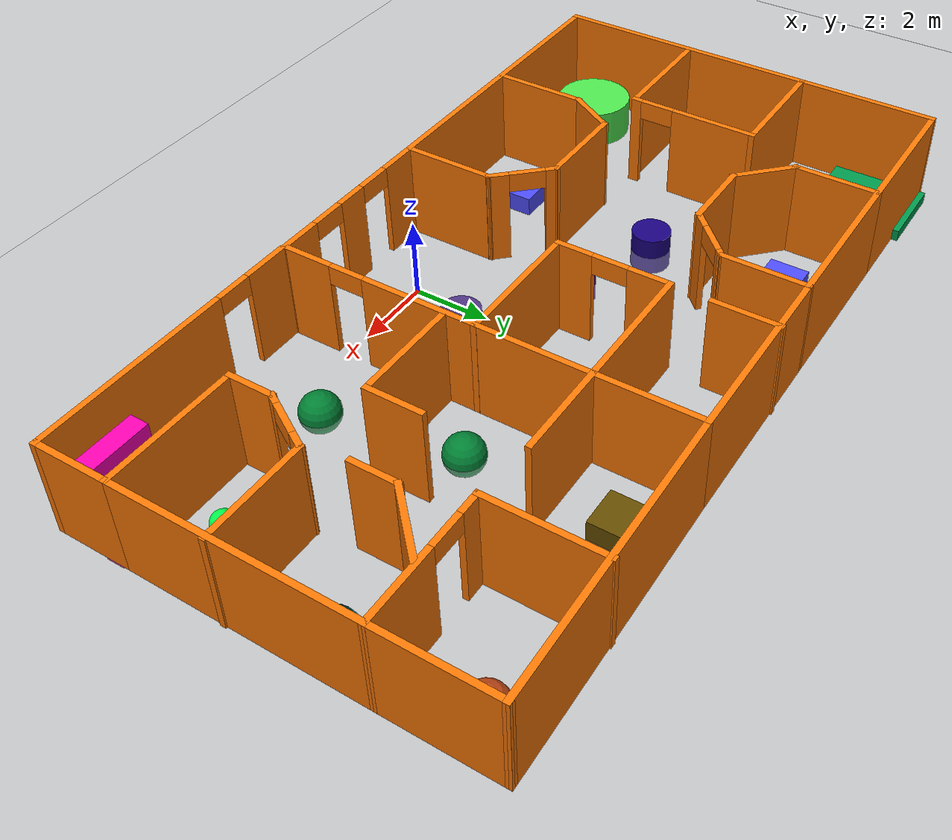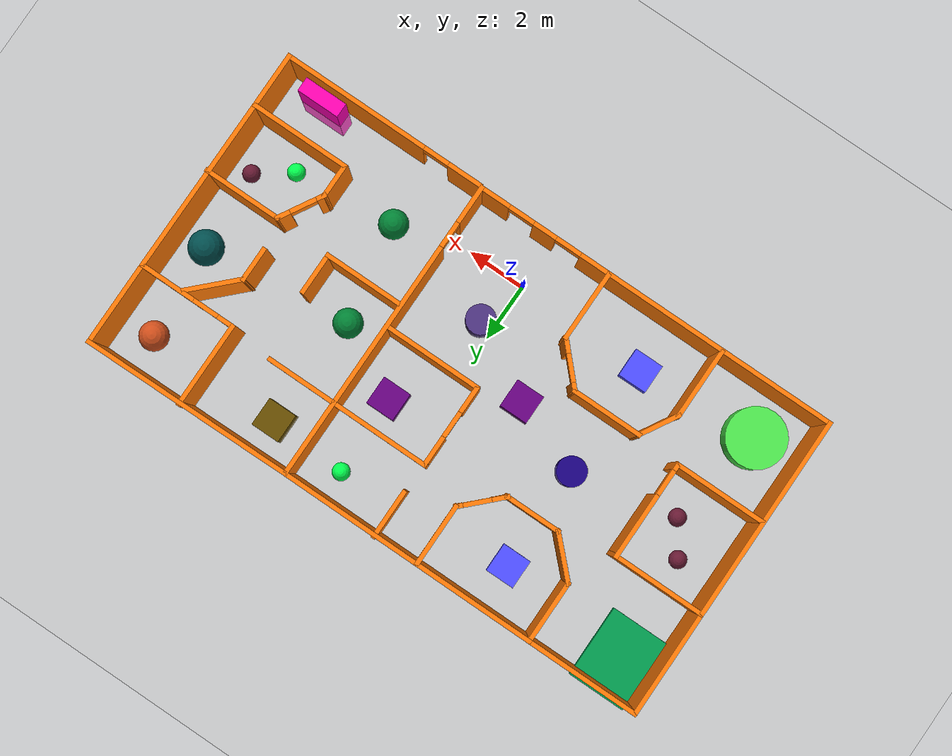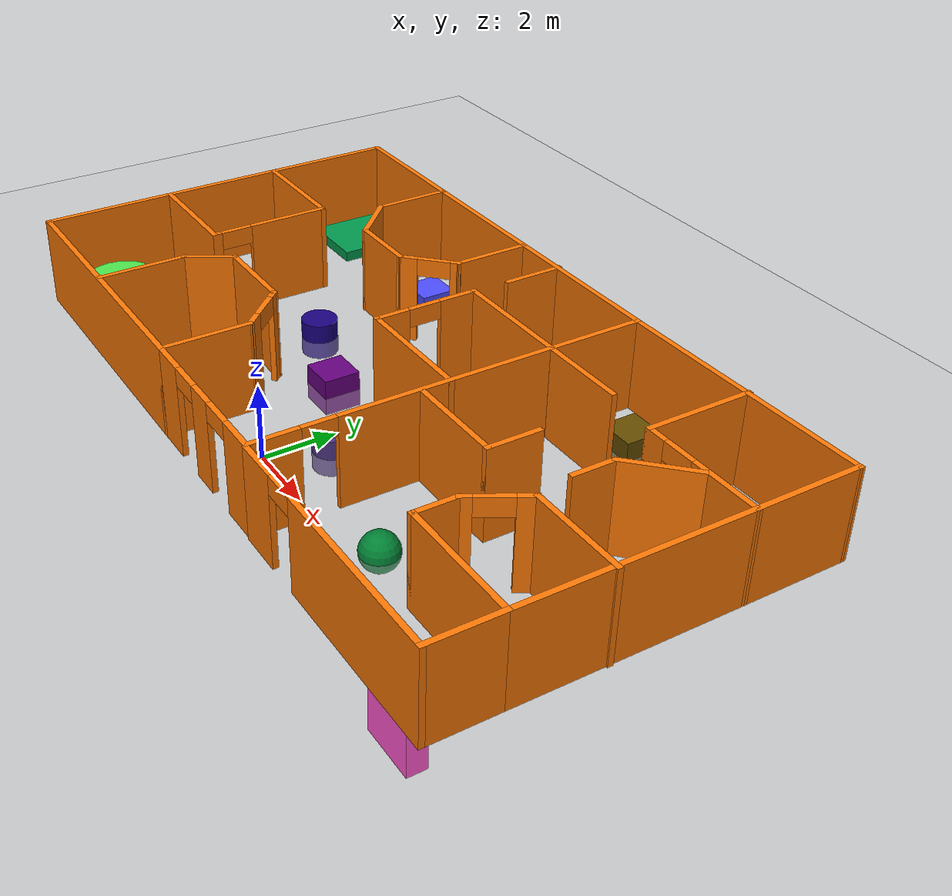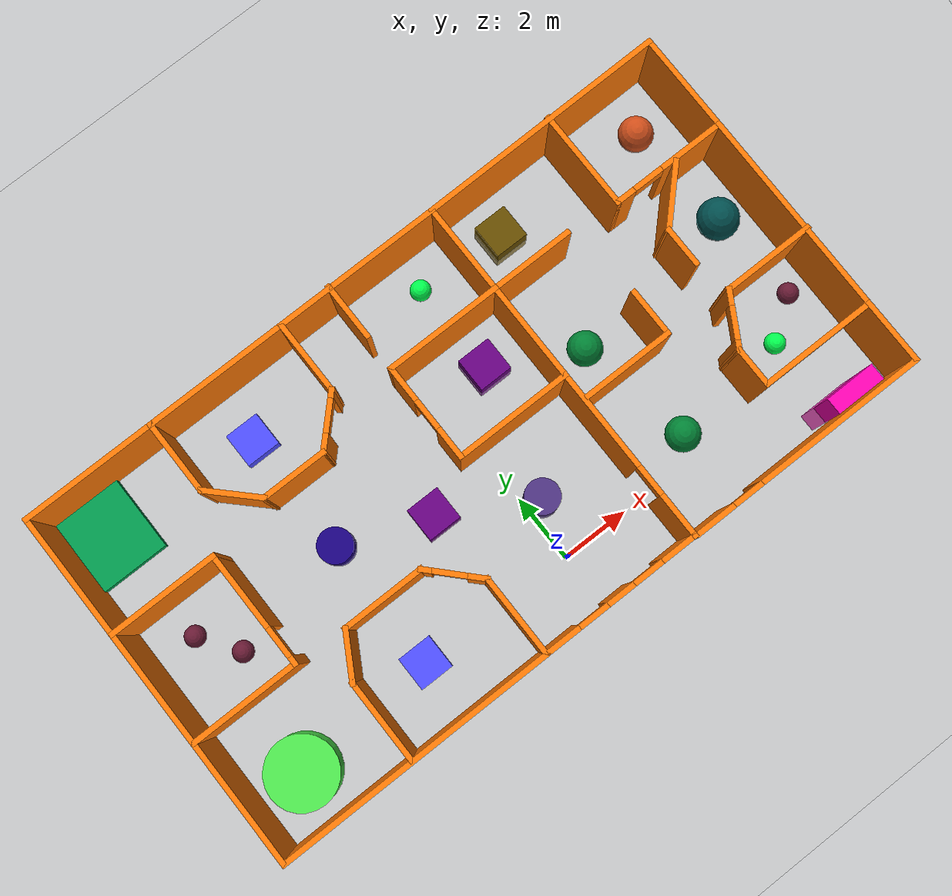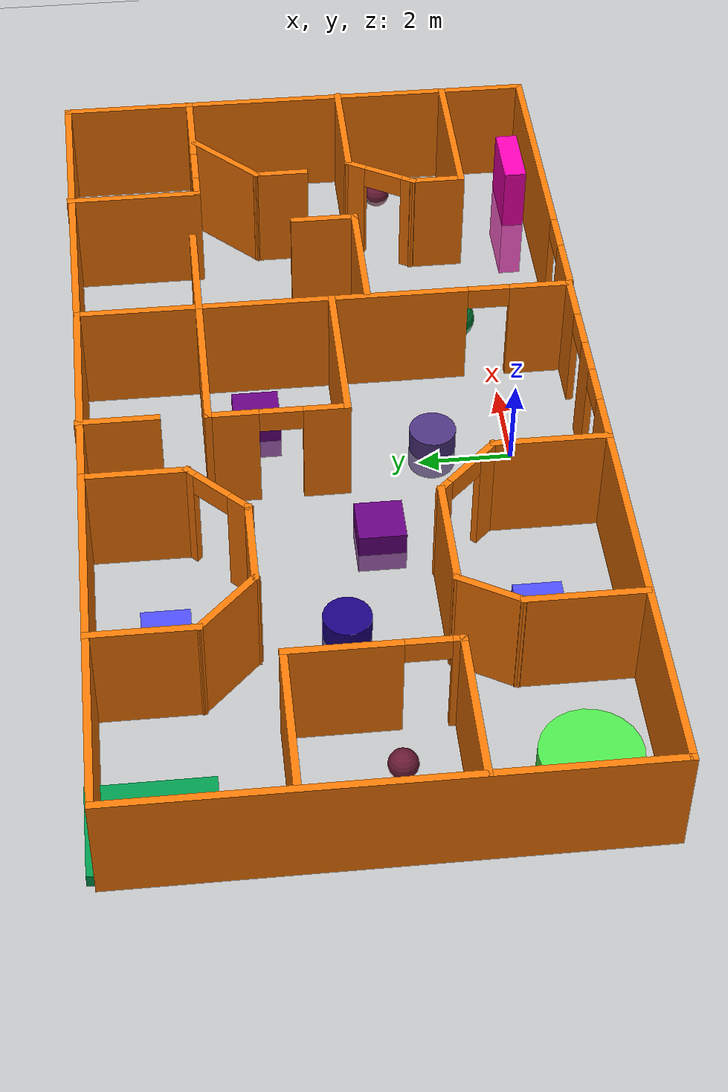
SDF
<sdf version="1.7">
 <world name="default">
  <light name="sun" type="directional">
   <pose>0 0 10 0 -0 0</pose>
   <diffuse>0.8 0.8 0.8 1</diffuse>
   <specular>0.2 0.2 0.2 1</specular>
   <attenuation>
    <range>1000</range>
    <constant>0.9</constant>
    <linear>0.01</linear>
    <quadratic>0.001</quadratic>
   </attenuation>
   <direction>-0.5 0.1 -0.9</direction>
   <spot><inner_angle>0</inner_angle><outer_angle>0</outer_angle><falloff>0</falloff></spot>
  </light>
  <model name="ground_plane">
   <static>1</static>
   <link name="link">
    <collision name="collision">
     <geometry><plane><normal>0 0 1</normal><size>100 100</size></plane></geometry>
     <surface><friction><ode><mu>100</mu><mu2>50</mu2></ode></friction></surface>
    </collision>
    <visual name="visual">
     <cast_shadows>0</cast_shadows>
     <geometry><plane><normal>0 0 1</normal><size>100 100</size></plane></geometry>
     <material>
      <script><uri>file://media/materials/scripts/gazebo.material</uri><name>Gazebo/Grey</name></script>
     </material>
    </visual>
   </link>
  </model>
  <gravity>0 0 -9.8</gravity>
  <magnetic_field>6e-06 2.3e-05 -4.2e-05</magnetic_field>
  <atmosphere type="adiabatic"/>
  <physics type="ode">
   <max_step_size>0.001</max_step_size>
   <real_time_factor>1</real_time_factor>
   <real_time_update_rate>1000</real_time_update_rate>
  </physics>
  <scene><ambient>0.4 0.4 0.4 1</ambient><background>0.7 0.7 0.7 1</background><shadows>1</shadows></scene>
  <spherical_coordinates>
   <surface_model>EARTH_WGS84</surface_model>
   <latitude_deg>0</latitude_deg>
   <longitude_deg>0</longitude_deg>
   <elevation>0</elevation>
   <heading_deg>0</heading_deg>
  </spherical_coordinates>
  <model name="nha1">
   <pose>-0.116735 3.77393 0 0 -0 0</pose>
   <link name="Wall_29">
    <collision name="Wall_29_Collision">
     <geometry><box><size>10.75 0.15 2.5</size></box></geometry>
     <pose>0 0 1.25 0 -0 0</pose>
    </collision>
    <visual name="Wall_29_Visual">
     <pose>0 0 1.25 0 -0 0</pose>
     <geometry><box><size>10.75 0.15 2.5</size></box></geometry>
     <material>
      <script><uri>file://media/materials/scripts/gazebo.material</uri><name>Gazebo/Grey</name></script>
      <ambient>0.996078 0.47451 0.0196078 1</ambient>
     </material>
     <meta><layer>0</layer></meta>
    </visual>
    <pose>-10.0315 -0.022957 0 0 -0 -1.5708</pose>
   </link>
   <link name="Wall_30">
    <collision name="Wall_30_Collision">
     <geometry><box><size>8.25 0.15 2.5</size></box></geometry>
     <pose>0 0 1.25 0 -0 0</pose>
    </collision>
    <visual name="Wall_30_Visual">
     <pose>0 0 1.25 0 -0 0</pose>
     <geometry><box><size>8.25 0.15 2.5</size></box></geometry>
     <material>
      <script><uri>file://media/materials/scripts/gazebo.material</uri><name>Gazebo/Grey</name></script>
      <ambient>0.996078 0.47451 0.0196078 1</ambient>
     </material>
     <meta><layer>0</layer></meta>
    </visual>
    <pose>-5.98146 -5.32296 0 0 -0 0</pose>
   </link>
   <link name="Wall_31">
    <collision name="Wall_31_Collision">
     <geometry><box><size>2.5 0.15 2.5</size></box></geometry>
     <pose>0 0 1.25 0 -0 0</pose>
    </collision>
    <visual name="Wall_31_Visual">
     <pose>0 0 1.25 0 -0 0</pose>
     <geometry><box><size>2.5 0.15 2.5</size></box></geometry>
     <material>
      <script><uri>file://media/materials/scripts/gazebo.material</uri><name>Gazebo/Grey</name></script>
      <ambient>0.996078 0.47451 0.0196078 1</ambient>
     </material>
     <meta><layer>0</layer></meta>
    </visual>
    <pose>-1.93146 -4.14796 0 0 -0 1.5708</pose>
   </link>
   <link name="Wall_34">
    <collision name="Wall_34_Collision">
     <geometry><box><size>2.5 0.15 2.5</size></box></geometry>
     <pose>0 0 1.25 0 -0 0</pose>
    </collision>
    <visual name="Wall_34_Visual">
     <pose>0 0 1.25 0 -0 0</pose>
     <geometry><box><size>2.5 0.15 2.5</size></box></geometry>
     <material>
      <script><uri>file://media/materials/scripts/gazebo.material</uri><name>Gazebo/Grey</name></script>
      <ambient>0.996078 0.47451 0.0196078 1</ambient>
     </material>
     <meta><layer>0</layer></meta>
    </visual>
    <pose>-6.10628 -4.10617 0 0 -0 1.5708</pose>
   </link>
   <link name="Wall_35">
    <collision name="Wall_35_Collision">
     <geometry><box><size>1.5 0.15 2.5</size></box></geometry>
     <pose>0 0 1.25 0 -0 0</pose>
    </collision>
    <visual name="Wall_35_Visual">
     <pose>0 0 1.25 0 -0 0</pose>
     <geometry><box><size>1.5 0.15 2.5</size></box></geometry>
     <material>
      <script><uri>file://media/materials/scripts/gazebo.material</uri><name>Gazebo/Grey</name></script>
      <ambient>0.996078 0.47451 0.0196078 1</ambient>
     </material>
     <meta><layer>0</layer></meta>
    </visual>
    <pose>-5.76878 -2.3466 0 0 -0 1.0472</pose>
   </link>
   <link name="Wall_36">
    <collision name="Wall_36_Collision">
     <geometry><box><size>2.5 0.15 2.5</size></box></geometry>
     <pose>0 0 1.25 0 -0 0</pose>
    </collision>
    <visual name="Wall_36_Visual">
     <pose>0 0 1.25 0 -0 0</pose>
     <geometry><box><size>2.5 0.15 2.5</size></box></geometry>
     <material>
      <script><uri>file://media/materials/scripts/gazebo.material</uri><name>Gazebo/Grey</name></script>
      <ambient>0.996078 0.47451 0.0196078 1</ambient>
     </material>
     <meta><layer>0</layer></meta>
    </visual>
    <pose>-4.25628 -1.76203 0 0 -0 0</pose>
   </link>
   <link name="Wall_37">
    <pose>-2.50637 -2.36749 0 0 -0 -0.811277</pose>
    <visual name="Wall_37_Visual_0">
     <pose>-0.735279 0 1.25 0 -0 0</pose>
     <geometry><box><size>0.349295 0.15 2.5</size></box></geometry>
     <material>
      <script><uri>file://media/materials/scripts/gazebo.material</uri><name>Gazebo/Grey</name></script>
      <ambient>0.996078 0.47451 0.0196078 1</ambient>
     </material>
     <meta><layer>0</layer></meta>
    </visual>
    <collision name="Wall_37_Collision_0">
     <geometry><box><size>0.349295 0.15 2.5</size></box></geometry>
     <pose>-0.735279 0 1.25 0 -0 0</pose>
    </collision>
    <visual name="Wall_37_Visual_1">
     <pose>0.624647 0 1.25 0 -0 0</pose>
     <geometry><box><size>0.570559 0.15 2.5</size></box></geometry>
     <material>
      <script><uri>file://media/materials/scripts/gazebo.material</uri><name>Gazebo/Grey</name></script>
      <ambient>0.996078 0.47451 0.0196078 1</ambient>
     </material>
     <meta><layer>0</layer></meta>
    </visual>
    <collision name="Wall_37_Collision_1">
     <geometry><box><size>0.570559 0.15 2.5</size></box></geometry>
     <pose>0.624647 0 1.25 0 -0 0</pose>
    </collision>
    <visual name="Wall_37_Visual_2">
     <pose>-0.110632 0 2.25 0 -0 0</pose>
     <geometry><box><size>0.9 0.15 0.5</size></box></geometry>
     <material>
      <script><uri>file://media/materials/scripts/gazebo.material</uri><name>Gazebo/Grey</name></script>
      <ambient>0.996078 0.47451 0.0196078 1</ambient>
     </material>
     <meta><layer>0</layer></meta>
    </visual>
    <collision name="Wall_37_Collision_2">
     <geometry><box><size>0.9 0.15 0.5</size></box></geometry>
     <pose>-0.110632 0 2.25 0 -0 0</pose>
    </collision>
   </link>
   <link name="Wall_43">
    <collision name="Wall_43_Collision">
     <geometry><box><size>3.25 0.15 2.5</size></box></geometry>
     <pose>0 0 1.25 0 -0 0</pose>
    </collision>
    <visual name="Wall_43_Visual">
     <pose>0 0 1.25 0 -0 0</pose>
     <geometry><box><size>3.25 0.15 2.5</size></box></geometry>
     <material>
      <script><uri>file://media/materials/scripts/gazebo.material</uri><name>Gazebo/Grey</name></script>
      <ambient>0.996078 0.47451 0.0196078 1</ambient>
     </material>
     <meta><layer>0</layer></meta>
    </visual>
    <pose>-8.47405 -1.67822 0 0 -0 0</pose>
   </link>
   <link name="Wall_44">
    <pose>-6.92405 -0.003215 0 0 -0 1.5708</pose>
    <visual name="Wall_44_Visual_0">
     <pose>-1.60946 0 1.25 0 -0 0</pose>
     <geometry><box><size>0.281077 0.15 2.5</size></box></geometry>
     <material>
      <script><uri>file://media/materials/scripts/gazebo.material</uri><name>Gazebo/Grey</name></script>
      <ambient>0.996078 0.47451 0.0196078 1</ambient>
     </material>
     <meta><layer>0</layer></meta>
    </visual>
    <collision name="Wall_44_Collision_0">
     <geometry><box><size>0.281077 0.15 2.5</size></box></geometry>
     <pose>-1.60946 0 1.25 0 -0 0</pose>
    </collision>
    <visual name="Wall_44_Visual_1">
     <pose>0.590538 0 1.25 0 -0 0</pose>
     <geometry><box><size>2.31892 0.15 2.5</size></box></geometry>
     <material>
      <script><uri>file://media/materials/scripts/gazebo.material</uri><name>Gazebo/Grey</name></script>
      <ambient>0.996078 0.47451 0.0196078 1</ambient>
     </material>
     <meta><layer>0</layer></meta>
    </visual>
    <collision name="Wall_44_Collision_1">
     <geometry><box><size>2.31892 0.15 2.5</size></box></geometry>
     <pose>0.590538 0 1.25 0 -0 0</pose>
    </collision>
    <visual name="Wall_44_Visual_2">
     <pose>-1.01892 0 2.25 0 -0 0</pose>
     <geometry><box><size>0.9 0.15 0.5</size></box></geometry>
     <material>
      <script><uri>file://media/materials/scripts/gazebo.material</uri><name>Gazebo/Grey</name></script>
      <ambient>0.996078 0.47451 0.0196078 1</ambient>
     </material>
     <meta><layer>0</layer></meta>
    </visual>
    <collision name="Wall_44_Collision_2">
     <geometry><box><size>0.9 0.15 0.5</size></box></geometry>
     <pose>-1.01892 0 2.25 0 -0 0</pose>
    </collision>
   </link>
   <link name="Wall_45">
    <collision name="Wall_45_Collision">
     <geometry><box><size>3.25 0.15 2.5</size></box></geometry>
     <pose>0 0 1.25 0 -0 0</pose>
    </collision>
    <visual name="Wall_45_Visual">
     <pose>0 0 1.25 0 -0 0</pose>
     <geometry><box><size>3.25 0.15 2.5</size></box></geometry>
     <material>
      <script><uri>file://media/materials/scripts/gazebo.material</uri><name>Gazebo/Grey</name></script>
      <ambient>0.996078 0.47451 0.0196078 1</ambient>
     </material>
     <meta><layer>0</layer></meta>
    </visual>
    <pose>-8.47405 1.67179 0 0 -0 3.14159</pose>
   </link>
   <link name="Wall_47">
    <collision name="Wall_47_Collision">
     <geometry><box><size>4 0.15 2.5</size></box></geometry>
     <pose>0 0 1.25 0 -0 0</pose>
    </collision>
    <visual name="Wall_47_Visual">
     <pose>0 0 1.25 0 -0 0</pose>
     <geometry><box><size>4 0.15 2.5</size></box></geometry>
     <material>
      <script><uri>file://media/materials/scripts/gazebo.material</uri><name>Gazebo/Grey</name></script>
      <ambient>0.996078 0.47451 0.0196078 1</ambient>
     </material>
     <meta><layer>0</layer></meta>
    </visual>
    <pose>-8.10646 5.27704 0 0 -0 0</pose>
   </link>
   <link name="Wall_48">
    <collision name="Wall_48_Collision">
     <geometry><box><size>2.25 0.15 2.5</size></box></geometry>
     <pose>0 0 1.25 0 -0 0</pose>
    </collision>
    <visual name="Wall_48_Visual">
     <pose>0 0 1.25 0 -0 0</pose>
     <geometry><box><size>2.25 0.15 2.5</size></box></geometry>
     <material>
      <script><uri>file://media/materials/scripts/gazebo.material</uri><name>Gazebo/Grey</name></script>
      <ambient>0.996078 0.47451 0.0196078 1</ambient>
     </material>
     <meta><layer>0</layer></meta>
    </visual>
    <pose>-6.18146 4.22704 0 0 -0 -1.5708</pose>
   </link>
   <link name="Wall_49">
    <collision name="Wall_49_Collision">
     <geometry><box><size>1.75 0.15 2.5</size></box></geometry>
     <pose>0 0 1.25 0 -0 0</pose>
    </collision>
    <visual name="Wall_49_Visual">
     <pose>0 0 1.25 0 -0 0</pose>
     <geometry><box><size>1.75 0.15 2.5</size></box></geometry>
     <material>
      <script><uri>file://media/materials/scripts/gazebo.material</uri><name>Gazebo/Grey</name></script>
      <ambient>0.996078 0.47451 0.0196078 1</ambient>
     </material>
     <meta><layer>0</layer></meta>
    </visual>
    <pose>-5.61578 2.61136 0 0 -0 -0.785398</pose>
   </link>
   <link name="Wall_50">
    <collision name="Wall_50_Collision">
     <geometry><box><size>2 0.15 2.5</size></box></geometry>
     <pose>0 0 1.25 0 -0 0</pose>
    </collision>
    <visual name="Wall_50_Visual">
     <pose>0 0 1.25 0 -0 0</pose>
     <geometry><box><size>2 0.15 2.5</size></box></geometry>
     <material>
      <script><uri>file://media/materials/scripts/gazebo.material</uri><name>Gazebo/Grey</name></script>
      <ambient>0.996078 0.47451 0.0196078 1</ambient>
     </material>
     <meta><layer>0</layer></meta>
    </visual>
    <pose>-4.12509 2.04567 0 0 -0 0</pose>
   </link>
   <link name="Wall_51">
    <pose>-2.63441 2.61136 0 0 -0 0.785398</pose>
    <visual name="Wall_51_Visual_0">
     <pose>-0.594056 0 1.25 0 -0 0</pose>
     <geometry><box><size>0.561887 0.15 2.5</size></box></geometry>
     <material>
      <script><uri>file://media/materials/scripts/gazebo.material</uri><name>Gazebo/Grey</name></script>
      <ambient>0.996078 0.47451 0.0196078 1</ambient>
     </material>
     <meta><layer>0</layer></meta>
    </visual>
    <collision name="Wall_51_Collision_0">
     <geometry><box><size>0.561887 0.15 2.5</size></box></geometry>
     <pose>-0.594056 0 1.25 0 -0 0</pose>
    </collision>
    <visual name="Wall_51_Visual_1">
     <pose>0.730944 0 1.25 0 -0 0</pose>
     <geometry><box><size>0.288113 0.15 2.5</size></box></geometry>
     <material>
      <script><uri>file://media/materials/scripts/gazebo.material</uri><name>Gazebo/Grey</name></script>
      <ambient>0.996078 0.47451 0.0196078 1</ambient>
     </material>
     <meta><layer>0</layer></meta>
    </visual>
    <collision name="Wall_51_Collision_1">
     <geometry><box><size>0.288113 0.15 2.5</size></box></geometry>
     <pose>0.730944 0 1.25 0 -0 0</pose>
    </collision>
    <visual name="Wall_51_Visual_2">
     <pose>0.136887 0 2.25 0 -0 0</pose>
     <geometry><box><size>0.9 0.15 0.5</size></box></geometry>
     <material>
      <script><uri>file://media/materials/scripts/gazebo.material</uri><name>Gazebo/Grey</name></script>
      <ambient>0.996078 0.47451 0.0196078 1</ambient>
     </material>
     <meta><layer>0</layer></meta>
    </visual>
    <collision name="Wall_51_Collision_2">
     <geometry><box><size>0.9 0.15 0.5</size></box></geometry>
     <pose>0.136887 0 2.25 0 -0 0</pose>
    </collision>
   </link>
   <link name="Wall_52">
    <collision name="Wall_52_Collision">
     <geometry><box><size>2.25 0.15 2.5</size></box></geometry>
     <pose>0 0 1.25 0 -0 0</pose>
    </collision>
    <visual name="Wall_52_Visual">
     <pose>0 0 1.25 0 -0 0</pose>
     <geometry><box><size>2.25 0.15 2.5</size></box></geometry>
     <material>
      <script><uri>file://media/materials/scripts/gazebo.material</uri><name>Gazebo/Grey</name></script>
      <ambient>0.996078 0.47451 0.0196078 1</ambient>
     </material>
     <meta><layer>0</layer></meta>
    </visual>
    <pose>-2.06872 4.22704 0 0 -0 1.5708</pose>
   </link>
   <link name="Wall_53">
    <collision name="Wall_53_Collision">
     <geometry><box><size>4.26274 0.15 2.5</size></box></geometry>
     <pose>0 0 1.25 0 -0 0</pose>
    </collision>
    <visual name="Wall_53_Visual">
     <pose>0 0 1.25 0 -0 0</pose>
     <geometry><box><size>4.26274 0.15 2.5</size></box></geometry>
     <material>
      <script><uri>file://media/materials/scripts/gazebo.material</uri><name>Gazebo/Grey</name></script>
      <ambient>0.996078 0.47451 0.0196078 1</ambient>
     </material>
     <meta><layer>0</layer></meta>
    </visual>
    <pose>-4.12509 5.27704 0 0 -0 3.14159</pose>
   </link>
   <link name="Wall_55">
    <collision name="Wall_55_Collision">
     <geometry><box><size>5 0.15 2.5</size></box></geometry>
     <pose>0 0 1.25 0 -0 0</pose>
    </collision>
    <visual name="Wall_55_Visual">
     <pose>0 0 1.25 0 -0 0</pose>
     <geometry><box><size>5 0.15 2.5</size></box></geometry>
     <material>
      <script><uri>file://media/materials/scripts/gazebo.material</uri><name>Gazebo/Grey</name></script>
      <ambient>0.996078 0.47451 0.0196078 1</ambient>
     </material>
     <meta><layer>0</layer></meta>
    </visual>
    <pose>0.356279 5.27704 0 0 -0 0</pose>
   </link>
   <link name="Wall_59">
    <pose>2.78128 -0.022957 0 0 -0 -1.5708</pose>
    <visual name="Wall_59_Visual_0">
     <pose>-1.13822 0 1.25 0 -0 0</pose>
     <geometry><box><size>8.47355 0.15 2.5</size></box></geometry>
     <material>
      <script><uri>file://media/materials/scripts/gazebo.material</uri><name>Gazebo/Grey</name></script>
      <ambient>0.996078 0.47451 0.0196078 1</ambient>
     </material>
     <meta><layer>0</layer></meta>
    </visual>
    <collision name="Wall_59_Collision_0">
     <geometry><box><size>8.47355 0.15 2.5</size></box></geometry>
     <pose>-1.13822 0 1.25 0 -0 0</pose>
    </collision>
    <visual name="Wall_59_Visual_1">
     <pose>4.68678 0 1.25 0 -0 0</pose>
     <geometry><box><size>1.37644 0.15 2.5</size></box></geometry>
     <material>
      <script><uri>file://media/materials/scripts/gazebo.material</uri><name>Gazebo/Grey</name></script>
      <ambient>0.996078 0.47451 0.0196078 1</ambient>
     </material>
     <meta><layer>0</layer></meta>
    </visual>
    <collision name="Wall_59_Collision_1">
     <geometry><box><size>1.37644 0.15 2.5</size></box></geometry>
     <pose>4.68678 0 1.25 0 -0 0</pose>
    </collision>
    <visual name="Wall_59_Visual_2">
     <pose>3.54855 0 2.25 0 -0 0</pose>
     <geometry><box><size>0.9 0.15 0.5</size></box></geometry>
     <material>
      <script><uri>file://media/materials/scripts/gazebo.material</uri><name>Gazebo/Grey</name></script>
      <ambient>0.996078 0.47451 0.0196078 1</ambient>
     </material>
     <meta><layer>0</layer></meta>
    </visual>
    <collision name="Wall_59_Collision_2">
     <geometry><box><size>0.9 0.15 0.5</size></box></geometry>
     <pose>3.54855 0 2.25 0 -0 0</pose>
    </collision>
   </link>
   <link name="Wall_60">
    <pose>0.481279 -5.32296 0 0 -0 3.14159</pose>
    <visual name="Wall_60_Visual_0">
     <pose>-1.81928 0 1.25 0 -0 0</pose>
     <geometry><box><size>1.11145 0.15 2.5</size></box></geometry>
     <material>
      <script><uri>file://media/materials/scripts/gazebo.material</uri><name>Gazebo/Grey</name></script>
      <ambient>0.996078 0.47451 0.0196078 1</ambient>
     </material>
     <meta><layer>0</layer></meta>
    </visual>
    <collision name="Wall_60_Collision_0">
     <geometry><box><size>1.11145 0.15 2.5</size></box></geometry>
     <pose>-1.81928 0 1.25 0 -0 0</pose>
    </collision>
    <visual name="Wall_60_Visual_1">
     <pose>0.050953 0 1.25 0 -0 0</pose>
     <geometry><box><size>0.829013 0.15 2.5</size></box></geometry>
     <material>
      <script><uri>file://media/materials/scripts/gazebo.material</uri><name>Gazebo/Grey</name></script>
      <ambient>0.996078 0.47451 0.0196078 1</ambient>
     </material>
     <meta><layer>0</layer></meta>
    </visual>
    <collision name="Wall_60_Collision_1">
     <geometry><box><size>0.829013 0.15 2.5</size></box></geometry>
     <pose>0.050953 0 1.25 0 -0 0</pose>
    </collision>
    <visual name="Wall_60_Visual_2">
     <pose>1.87023 0 1.25 0 -0 0</pose>
     <geometry><box><size>1.00954 0.15 2.5</size></box></geometry>
     <material>
      <script><uri>file://media/materials/scripts/gazebo.material</uri><name>Gazebo/Grey</name></script>
      <ambient>0.996078 0.47451 0.0196078 1</ambient>
     </material>
     <meta><layer>0</layer></meta>
    </visual>
    <collision name="Wall_60_Collision_2">
     <geometry><box><size>1.00954 0.15 2.5</size></box></geometry>
     <pose>1.87023 0 1.25 0 -0 0</pose>
    </collision>
    <visual name="Wall_60_Visual_3">
     <pose>-0.813553 0 2.25 0 -0 0</pose>
     <geometry><box><size>0.9 0.15 0.5</size></box></geometry>
     <material>
      <script><uri>file://media/materials/scripts/gazebo.material</uri><name>Gazebo/Grey</name></script>
      <ambient>0.996078 0.47451 0.0196078 1</ambient>
     </material>
     <meta><layer>0</layer></meta>
    </visual>
    <collision name="Wall_60_Collision_3">
     <geometry><box><size>0.9 0.15 0.5</size></box></geometry>
     <pose>-0.813553 0 2.25 0 -0 0</pose>
    </collision>
    <visual name="Wall_60_Visual_4">
     <pose>0.91546 0 2.25 0 -0 0</pose>
     <geometry><box><size>0.9 0.15 0.5</size></box></geometry>
     <material>
      <script><uri>file://media/materials/scripts/gazebo.material</uri><name>Gazebo/Grey</name></script>
      <ambient>0.996078 0.47451 0.0196078 1</ambient>
     </material>
     <meta><layer>0</layer></meta>
    </visual>
    <collision name="Wall_60_Collision_4">
     <geometry><box><size>0.9 0.15 0.5</size></box></geometry>
     <pose>0.91546 0 2.25 0 -0 0</pose>
    </collision>
   </link>
   <link name="Wall_62">
    <collision name="Wall_62_Collision">
     <geometry><box><size>1.75 0.15 2.5</size></box></geometry>
     <pose>0 0 1.25 0 -0 0</pose>
    </collision>
    <visual name="Wall_62_Visual">
     <pose>0 0 1.25 0 -0 0</pose>
     <geometry><box><size>1.75 0.15 2.5</size></box></geometry>
     <material>
      <script><uri>file://media/materials/scripts/gazebo.material</uri><name>Gazebo/Grey</name></script>
      <ambient>0.996078 0.47451 0.0196078 1</ambient>
     </material>
     <meta><layer>0</layer></meta>
    </visual>
    <pose>-0.522165 4.51594 0 0 -0 -1.5708</pose>
   </link>
   <link name="Wall_64">
    <collision name="Wall_64_Collision">
     <geometry><box><size>3.5 0.15 2.5</size></box></geometry>
     <pose>0 0 1.25 0 -0 0</pose>
    </collision>
    <visual name="Wall_64_Visual">
     <pose>0 0 1.25 0 -0 0</pose>
     <geometry><box><size>3.5 0.15 2.5</size></box></geometry>
     <material>
      <script><uri>file://media/materials/scripts/gazebo.material</uri><name>Gazebo/Grey</name></script>
      <ambient>0.996078 0.47451 0.0196078 1</ambient>
     </material>
     <meta><layer>0</layer></meta>
    </visual>
    <pose>1.10964 2.67753 0 0 -0 3.14159</pose>
   </link>
   <link name="Wall_65">
    <pose>-0.565362 1.25253 0 0 -0 -1.5708</pose>
    <visual name="Wall_65_Visual_0">
     <pose>-0.943697 0 1.25 0 -0 0</pose>
     <geometry><box><size>1.11261 0.15 2.5</size></box></geometry>
     <material>
      <script><uri>file://media/materials/scripts/gazebo.material</uri><name>Gazebo/Grey</name></script>
      <ambient>0.996078 0.47451 0.0196078 1</ambient>
     </material>
     <meta><layer>0</layer></meta>
    </visual>
    <collision name="Wall_65_Collision_0">
     <geometry><box><size>1.11261 0.15 2.5</size></box></geometry>
     <pose>-0.943697 0 1.25 0 -0 0</pose>
    </collision>
    <visual name="Wall_65_Visual_1">
     <pose>1.0063 0 1.25 0 -0 0</pose>
     <geometry><box><size>0.987394 0.15 2.5</size></box></geometry>
     <material>
      <script><uri>file://media/materials/scripts/gazebo.material</uri><name>Gazebo/Grey</name></script>
      <ambient>0.996078 0.47451 0.0196078 1</ambient>
     </material>
     <meta><layer>0</layer></meta>
    </visual>
    <collision name="Wall_65_Collision_1">
     <geometry><box><size>0.987394 0.15 2.5</size></box></geometry>
     <pose>1.0063 0 1.25 0 -0 0</pose>
    </collision>
    <visual name="Wall_65_Visual_2">
     <pose>0.062606 0 2.25 0 -0 0</pose>
     <geometry><box><size>0.9 0.15 0.5</size></box></geometry>
     <material>
      <script><uri>file://media/materials/scripts/gazebo.material</uri><name>Gazebo/Grey</name></script>
      <ambient>0.996078 0.47451 0.0196078 1</ambient>
     </material>
     <meta><layer>0</layer></meta>
    </visual>
    <collision name="Wall_65_Collision_2">
     <geometry><box><size>0.9 0.15 0.5</size></box></geometry>
     <pose>0.062606 0 2.25 0 -0 0</pose>
    </collision>
   </link>
   <link name="Wall_66">
    <collision name="Wall_66_Collision">
     <geometry><box><size>3.5 0.15 2.5</size></box></geometry>
     <pose>0 0 1.25 0 -0 0</pose>
    </collision>
    <visual name="Wall_66_Visual">
     <pose>0 0 1.25 0 -0 0</pose>
     <geometry><box><size>3.5 0.15 2.5</size></box></geometry>
     <material>
      <script><uri>file://media/materials/scripts/gazebo.material</uri><name>Gazebo/Grey</name></script>
      <ambient>0.996078 0.47451 0.0196078 1</ambient>
     </material>
     <meta><layer>0</layer></meta>
    </visual>
    <pose>1.10964 -0.17247 0 0 -0 0</pose>
   </link>
   <link name="Wall_68">
    <collision name="Wall_68_Collision">
     <geometry><box><size>3 0.15 2.5</size></box></geometry>
     <pose>0 0 1.25 0 -0 0</pose>
    </collision>
    <visual name="Wall_68_Visual">
     <pose>0 0 1.25 0 -0 0</pose>
     <geometry><box><size>3 0.15 2.5</size></box></geometry>
     <material>
      <script><uri>file://media/materials/scripts/gazebo.material</uri><name>Gazebo/Grey</name></script>
      <ambient>0.996078 0.47451 0.0196078 1</ambient>
     </material>
     <meta><layer>0</layer></meta>
    </visual>
    <pose>6.6543 3.92612 0 0 -0 -1.5708</pose>
   </link>
   <link name="Wall_71">
    <pose>8.3293 2.50112 0 0 -0 0</pose>
    <visual name="Wall_71_Visual_0">
     <pose>-1.43851 0 1.25 0 -0 0</pose>
     <geometry><box><size>0.622978 0.15 2.5</size></box></geometry>
     <material>
      <script><uri>file://media/materials/scripts/gazebo.material</uri><name>Gazebo/Grey</name></script>
      <ambient>0.996078 0.47451 0.0196078 1</ambient>
     </material>
     <meta><layer>0</layer></meta>
    </visual>
    <collision name="Wall_71_Collision_0">
     <geometry><box><size>0.622978 0.15 2.5</size></box></geometry>
     <pose>-1.43851 0 1.25 0 -0 0</pose>
    </collision>
    <visual name="Wall_71_Visual_1">
     <pose>0.761489 0 1.25 0 -0 0</pose>
     <geometry><box><size>1.97702 0.15 2.5</size></box></geometry>
     <material>
      <script><uri>file://media/materials/scripts/gazebo.material</uri><name>Gazebo/Grey</name></script>
      <ambient>0.996078 0.47451 0.0196078 1</ambient>
     </material>
     <meta><layer>0</layer></meta>
    </visual>
    <collision name="Wall_71_Collision_1">
     <geometry><box><size>1.97702 0.15 2.5</size></box></geometry>
     <pose>0.761489 0 1.25 0 -0 0</pose>
    </collision>
    <visual name="Wall_71_Visual_2">
     <pose>-0.677022 0 2.25 0 -0 0</pose>
     <geometry><box><size>0.9 0.15 0.5</size></box></geometry>
     <material>
      <script><uri>file://media/materials/scripts/gazebo.material</uri><name>Gazebo/Grey</name></script>
      <ambient>0.996078 0.47451 0.0196078 1</ambient>
     </material>
     <meta><layer>0</layer></meta>
    </visual>
    <collision name="Wall_71_Collision_2">
     <geometry><box><size>0.9 0.15 0.5</size></box></geometry>
     <pose>-0.677022 0 2.25 0 -0 0</pose>
    </collision>
   </link>
   <link name="Wall_72">
    <collision name="Wall_72_Collision">
     <geometry><box><size>3 0.15 2.5</size></box></geometry>
     <pose>0 0 1.25 0 -0 0</pose>
    </collision>
    <visual name="Wall_72_Visual">
     <pose>0 0 1.25 0 -0 0</pose>
     <geometry><box><size>3 0.15 2.5</size></box></geometry>
     <material>
      <script><uri>file://media/materials/scripts/gazebo.material</uri><name>Gazebo/Grey</name></script>
      <ambient>0.996078 0.47451 0.0196078 1</ambient>
     </material>
     <meta><layer>0</layer></meta>
    </visual>
    <pose>10.0043 3.92612 0 0 -0 1.5708</pose>
   </link>
   <link name="Wall_73">
    <collision name="Wall_73_Collision">
     <geometry><box><size>7.3734 0.15 2.5</size></box></geometry>
     <pose>0 0 1.25 0 -0 0</pose>
    </collision>
    <visual name="Wall_73_Visual">
     <pose>0 0 1.25 0 -0 0</pose>
     <geometry><box><size>7.3734 0.15 2.5</size></box></geometry>
     <material>
      <script><uri>file://media/materials/scripts/gazebo.material</uri><name>Gazebo/Grey</name></script>
      <ambient>0.996078 0.47451 0.0196078 1</ambient>
     </material>
     <meta><layer>0</layer></meta>
    </visual>
    <pose>6.39279 5.31408 0 0 -0 -3.13134</pose>
   </link>
   <link name="Wall_75">
    <collision name="Wall_75_Collision">
     <geometry><box><size>2 0.15 2.5</size></box></geometry>
     <pose>0 0 1.25 0 -0 0</pose>
    </collision>
    <visual name="Wall_75_Visual">
     <pose>0 0 1.25 0 -0 0</pose>
     <geometry><box><size>2 0.15 2.5</size></box></geometry>
     <material>
      <script><uri>file://media/materials/scripts/gazebo.material</uri><name>Gazebo/Grey</name></script>
      <ambient>0.996078 0.47451 0.0196078 1</ambient>
     </material>
     <meta><layer>0</layer></meta>
    </visual>
    <pose>7.8647 1.7772 0 0 -0 -2.35619</pose>
   </link>
   <link name="Wall_76">
    <collision name="Wall_76_Collision">
     <geometry><box><size>1.25 0.15 2.5</size></box></geometry>
     <pose>0 0 1.25 0 -0 0</pose>
    </collision>
    <visual name="Wall_76_Visual">
     <pose>0 0 1.25 0 -0 0</pose>
     <geometry><box><size>1.25 0.15 2.5</size></box></geometry>
     <material>
      <script><uri>file://media/materials/scripts/gazebo.material</uri><name>Gazebo/Grey</name></script>
      <ambient>0.996078 0.47451 0.0196078 1</ambient>
     </material>
     <meta><layer>0</layer></meta>
    </visual>
    <pose>7.21063 0.573131 0 0 -0 -1.5708</pose>
   </link>
   <link name="Wall_78">
    <collision name="Wall_78_Collision">
     <geometry><box><size>2.75 0.15 2.5</size></box></geometry>
     <pose>0 0 1.25 0 -0 0</pose>
    </collision>
    <visual name="Wall_78_Visual">
     <pose>0 0 1.25 0 -0 0</pose>
     <geometry><box><size>2.75 0.15 2.5</size></box></geometry>
     <material>
      <script><uri>file://media/materials/scripts/gazebo.material</uri><name>Gazebo/Grey</name></script>
      <ambient>0.996078 0.47451 0.0196078 1</ambient>
     </material>
     <meta><layer>0</layer></meta>
    </visual>
    <pose>8.73146 -1.01624 0 0 -0 3.14159</pose>
   </link>
   <link name="Wall_79">
    <pose>7.03146 -1.70906 0 0 -0 -2.0944</pose>
    <visual name="Wall_79_Visual_0">
     <pose>-0.622881 0 1.25 0 -0 0</pose>
     <geometry><box><size>0.504237 0.15 2.5</size></box></geometry>
     <material>
      <script><uri>file://media/materials/scripts/gazebo.material</uri><name>Gazebo/Grey</name></script>
      <ambient>0.996078 0.47451 0.0196078 1</ambient>
     </material>
     <meta><layer>0</layer></meta>
    </visual>
    <collision name="Wall_79_Collision_0">
     <geometry><box><size>0.504237 0.15 2.5</size></box></geometry>
     <pose>-0.622881 0 1.25 0 -0 0</pose>
    </collision>
    <visual name="Wall_79_Visual_1">
     <pose>0.702119 0 1.25 0 -0 0</pose>
     <geometry><box><size>0.345763 0.15 2.5</size></box></geometry>
     <material>
      <script><uri>file://media/materials/scripts/gazebo.material</uri><name>Gazebo/Grey</name></script>
      <ambient>0.996078 0.47451 0.0196078 1</ambient>
     </material>
     <meta><layer>0</layer></meta>
    </visual>
    <collision name="Wall_79_Collision_1">
     <geometry><box><size>0.345763 0.15 2.5</size></box></geometry>
     <pose>0.702119 0 1.25 0 -0 0</pose>
    </collision>
    <visual name="Wall_79_Visual_2">
     <pose>0.079237 0 2.25 0 -0 0</pose>
     <geometry><box><size>0.9 0.15 0.5</size></box></geometry>
     <material>
      <script><uri>file://media/materials/scripts/gazebo.material</uri><name>Gazebo/Grey</name></script>
      <ambient>0.996078 0.47451 0.0196078 1</ambient>
     </material>
     <meta><layer>0</layer></meta>
    </visual>
    <collision name="Wall_79_Collision_2">
     <geometry><box><size>0.9 0.15 0.5</size></box></geometry>
     <pose>0.079237 0 2.25 0 -0 0</pose>
    </collision>
   </link>
   <link name="Wall_82">
    <collision name="Wall_82_Collision">
     <geometry><box><size>1.25 0.15 2.5</size></box></geometry>
     <pose>0 0 1.25 0 -0 0</pose>
    </collision>
    <visual name="Wall_82_Visual">
     <pose>0 0 1.25 0 -0 0</pose>
     <geometry><box><size>1.25 0.15 2.5</size></box></geometry>
     <material>
      <script><uri>file://media/materials/scripts/gazebo.material</uri><name>Gazebo/Grey</name></script>
      <ambient>0.996078 0.47451 0.0196078 1</ambient>
     </material>
     <meta><layer>0</layer></meta>
    </visual>
    <pose>6.63146 -2.95188 0 0 -0 -1.5708</pose>
   </link>
   <link name="Wall_83">
    <collision name="Wall_83_Collision">
     <geometry><box><size>3.5 0.15 2.5</size></box></geometry>
     <pose>0 0 1.25 0 -0 0</pose>
    </collision>
    <visual name="Wall_83_Visual">
     <pose>0 0 1.25 0 -0 0</pose>
     <geometry><box><size>3.5 0.15 2.5</size></box></geometry>
     <material>
      <script><uri>file://media/materials/scripts/gazebo.material</uri><name>Gazebo/Grey</name></script>
      <ambient>0.996078 0.47451 0.0196078 1</ambient>
     </material>
     <meta><layer>0</layer></meta>
    </visual>
    <pose>8.30646 -3.50188 0 0 -0 0</pose>
   </link>
   <link name="Wall_84">
    <collision name="Wall_84_Collision">
     <geometry><box><size>6.15304 0.15 2.5</size></box></geometry>
     <pose>0 0 1.25 0 -0 0</pose>
    </collision>
    <visual name="Wall_84_Visual">
     <pose>0 0 1.25 0 -0 0</pose>
     <geometry><box><size>6.15304 0.15 2.5</size></box></geometry>
     <material>
      <script><uri>file://media/materials/scripts/gazebo.material</uri><name>Gazebo/Grey</name></script>
      <ambient>0.996078 0.47451 0.0196078 1</ambient>
     </material>
     <meta><layer>0</layer></meta>
    </visual>
    <pose>9.99288 -0.500383 0 0 -0 1.56699</pose>
   </link>
   <link name="Wall_88">
    <collision name="Wall_88_Collision">
     <geometry><box><size>2 0.15 2.5</size></box></geometry>
     <pose>0 0 1.25 0 -0 0</pose>
    </collision>
    <visual name="Wall_88_Visual">
     <pose>0 0 1.25 0 -0 0</pose>
     <geometry><box><size>2 0.15 2.5</size></box></geometry>
     <material>
      <script><uri>file://media/materials/scripts/gazebo.material</uri><name>Gazebo/Grey</name></script>
      <ambient>0.996078 0.47451 0.0196078 1</ambient>
     </material>
     <meta><layer>0</layer></meta>
    </visual>
    <pose>9.98146 -4.42688 0 0 -0 -1.5708</pose>
   </link>
   <link name="Wall_89">
    <pose>6.43146 -5.35188 0 0 -0 3.14159</pose>
    <visual name="Wall_89_Visual_0">
     <pose>-1.0652 0 1.25 0 -0 0</pose>
     <geometry><box><size>5.11961 0.15 2.5</size></box></geometry>
     <material>
      <script><uri>file://media/materials/scripts/gazebo.material</uri><name>Gazebo/Grey</name></script>
      <ambient>0.996078 0.47451 0.0196078 1</ambient>
     </material>
     <meta><layer>0</layer></meta>
    </visual>
    <collision name="Wall_89_Collision_0">
     <geometry><box><size>5.11961 0.15 2.5</size></box></geometry>
     <pose>-1.0652 0 1.25 0 -0 0</pose>
    </collision>
    <visual name="Wall_89_Visual_1">
     <pose>3.0098 0 1.25 0 -0 0</pose>
     <geometry><box><size>1.23039 0.15 2.5</size></box></geometry>
     <material>
      <script><uri>file://media/materials/scripts/gazebo.material</uri><name>Gazebo/Grey</name></script>
      <ambient>0.996078 0.47451 0.0196078 1</ambient>
     </material>
     <meta><layer>0</layer></meta>
    </visual>
    <collision name="Wall_89_Collision_1">
     <geometry><box><size>1.23039 0.15 2.5</size></box></geometry>
     <pose>3.0098 0 1.25 0 -0 0</pose>
    </collision>
    <visual name="Wall_89_Visual_2">
     <pose>1.94461 0 2.25 0 -0 0</pose>
     <geometry><box><size>0.9 0.15 0.5</size></box></geometry>
     <material>
      <script><uri>file://media/materials/scripts/gazebo.material</uri><name>Gazebo/Grey</name></script>
      <ambient>0.996078 0.47451 0.0196078 1</ambient>
     </material>
     <meta><layer>0</layer></meta>
    </visual>
    <collision name="Wall_89_Collision_2">
     <geometry><box><size>0.9 0.15 0.5</size></box></geometry>
     <pose>1.94461 0 2.25 0 -0 0</pose>
    </collision>
   </link>
   <link name="Wall_91">
    <collision name="Wall_91_Collision">
     <geometry><box><size>2.75 0.15 2.5</size></box></geometry>
     <pose>0 0 1.25 0 -0 0</pose>
    </collision>
    <visual name="Wall_91_Visual">
     <pose>0 0 1.25 0 -0 0</pose>
     <geometry><box><size>2.75 0.15 2.5</size></box></geometry>
     <material>
      <script><uri>file://media/materials/scripts/gazebo.material</uri><name>Gazebo/Grey</name></script>
      <ambient>0.996078 0.47451 0.0196078 1</ambient>
     </material>
     <meta><layer>0</layer></meta>
    </visual>
    <pose>4.19017 -0.945883 0 0 -0 0</pose>
   </link>
   <link name="Wall_92">
    <collision name="Wall_92_Collision">
     <geometry><box><size>1.5 0.15 2.5</size></box></geometry>
     <pose>0 0 1.25 0 -0 0</pose>
    </collision>
    <visual name="Wall_92_Visual">
     <pose>0 0 1.25 0 -0 0</pose>
     <geometry><box><size>1.5 0.15 2.5</size></box></geometry>
     <material>
      <script><uri>file://media/materials/scripts/gazebo.material</uri><name>Gazebo/Grey</name></script>
      <ambient>0.996078 0.47451 0.0196078 1</ambient>
     </material>
     <meta><layer>0</layer></meta>
    </visual>
    <pose>5.49017 -0.270883 0 0 -0 1.5708</pose>
   </link>
   <link name="Wall_95">
    <collision name="Wall_95_Collision">
     <geometry><box><size>2.5 0.15 2.5</size></box></geometry>
     <pose>0 0 1.25 0 -0 0</pose>
    </collision>
    <visual name="Wall_95_Visual">
     <pose>0 0 1.25 0 -0 0</pose>
     <geometry><box><size>2.5 0.15 2.5</size></box></geometry>
     <material>
      <script><uri>file://media/materials/scripts/gazebo.material</uri><name>Gazebo/Grey</name></script>
      <ambient>0.996078 0.47451 0.0196078 1</ambient>
     </material>
     <meta><layer>0</layer></meta>
    </visual>
    <pose>3.95964 2.67753 0 0 -0 0</pose>
   </link>
   <static>1</static>
  </model>
  <model name="bed">
   <link name="link">
    <inertial>
     <mass>1</mass>
     <inertia>
      <ixx>0.166667</ixx>
      <ixy>0</ixy>
      <ixz>0</ixz>
      <iyy>0.166667</iyy>
      <iyz>0</iyz>
      <izz>0.166667</izz>
     </inertia>
    </inertial>
    <visual name="visual">
     <geometry><box><size>2 2.5 0.3</size></box></geometry>
     <material>
      <script><name>Gazebo/Grey</name><uri>file://media/materials/scripts/gazebo.material</uri></script>
      <shader type="pixel"><normal_map>__default__</normal_map></shader>
      <ambient>0 0.6 0.3 1</ambient>
      <diffuse>0.7 0.7 0.7 1</diffuse>
      <specular>0.01 0.01 0.01 1</specular>
      <emissive>0 0 0 1</emissive>
     </material>
    </visual>
    <collision name="collision">
     <geometry><box><size>2 2.5 0.3</size></box></geometry>
     <surface>
      <friction>
       <ode><mu>1</mu><mu2>1</mu2><fdir1>0 0 0</fdir1><slip1>0</slip1><slip2>0</slip2></ode>
       <torsional>
        <coefficient>1</coefficient>
        <patch_radius>0</patch_radius>
        <surface_radius>0</surface_radius>
        <use_patch_radius>1</use_patch_radius>
        <ode><slip>0</slip></ode>
       </torsional>
      </friction>
      <bounce><restitution_coefficient>0</restitution_coefficient><threshold>1e+06</threshold></bounce>
      <contact>
       <collide_without_contact>0</collide_without_contact>
       <collide_without_contact_bitmask>1</collide_without_contact_bitmask>
       <collide_bitmask>1</collide_bitmask>
       <ode>
        <soft_cfm>0</soft_cfm>
        <soft_erp>0.2</soft_erp>
        <kp>1e+13</kp>
        <kd>1</kd>
        <max_vel>0.01</max_vel>
        <min_depth>0</min_depth>
       </ode>
       <bullet>
        <split_impulse>1</split_impulse>
        <split_impulse_penetration_threshold>-0.01</split_impulse_penetration_threshold>
        <soft_cfm>0</soft_cfm>
        <soft_erp>0.2</soft_erp>
        <kp>1e+13</kp>
        <kd>1</kd>
       </bullet>
      </contact>
     </surface>
    </collision>
   </link>
   <static>0</static>
   <pose>-9.08934 8.03274 0.146251 -1e-05 0 0</pose>
  </model>
  <model name="unit_sphere777">
   <link name="link">
    <inertial>
     <mass>1</mass>
     <inertia><ixx>0.1</ixx><ixy>0</ixy><ixz>0</ixz><iyy>0.1</iyy><iyz>0</iyz><izz>0.1</izz></inertia>
    </inertial>
    <visual name="visual">
     <geometry><sphere><radius>0.3</radius></sphere></geometry>
     <material>
      <script><name>Gazebo/Grey</name><uri>file://media/materials/scripts/gazebo.material</uri></script>
      <shader type="pixel"><normal_map>__default__</normal_map></shader>
      <ambient>0.4 0.1 0.2 0</ambient>
      <diffuse>0.7 0.7 0.7 1</diffuse>
      <specular>0.01 0.01 0.01 1</specular>
      <emissive>0 0 0 1</emissive>
     </material>
    </visual>
    <collision name="collision">
     <geometry><sphere><radius>0.3</radius></sphere></geometry>
     <surface>
      <friction>
       <ode><mu>1</mu><mu2>1</mu2><fdir1>0 0 0</fdir1><slip1>0</slip1><slip2>0</slip2></ode>
       <torsional>
        <coefficient>1</coefficient>
        <patch_radius>0</patch_radius>
        <surface_radius>0</surface_radius>
        <use_patch_radius>1</use_patch_radius>
        <ode><slip>0</slip></ode>
       </torsional>
      </friction>
      <bounce><restitution_coefficient>0</restitution_coefficient><threshold>1e+06</threshold></bounce>
      <contact>
       <collide_without_contact>0</collide_without_contact>
       <collide_without_contact_bitmask>1</collide_without_contact_bitmask>
       <collide_bitmask>1</collide_bitmask>
       <ode>
        <soft_cfm>0</soft_cfm>
        <soft_erp>0.2</soft_erp>
        <kp>1e+13</kp>
        <kd>1</kd>
        <max_vel>0.01</max_vel>
        <min_depth>0</min_depth>
       </ode>
       <bullet>
        <split_impulse>1</split_impulse>
        <split_impulse_penetration_threshold>-0.01</split_impulse_penetration_threshold>
        <soft_cfm>0</soft_cfm>
        <soft_erp>0.2</soft_erp>
        <kp>1e+13</kp>
        <kd>1</kd>
       </bullet>
      </contact>
     </surface>
    </collision>
   </link>
   <static>0</static>
   <pose>-8.89889 4.39773 0.302461 0 -0 0</pose>
  </model>
  <model name="unit_sphere777_clone">
   <link name="link">
    <inertial>
     <mass>1</mass>
     <inertia><ixx>0.1</ixx><ixy>0</ixy><ixz>0</ixz><iyy>0.1</iyy><iyz>0</iyz><izz>0.1</izz></inertia>
    </inertial>
    <visual name="visual">
     <geometry><sphere><radius>0.3</radius></sphere></geometry>
     <material>
      <script><name>Gazebo/Grey</name><uri>file://media/materials/scripts/gazebo.material</uri></script>
      <shader type="pixel"><normal_map>__default__</normal_map></shader>
      <ambient>0.4 0.1 0.2 0</ambient>
      <diffuse>0.7 0.7 0.7 1</diffuse>
      <specular>0.01 0.01 0.01 1</specular>
      <emissive>0 0 0 1</emissive>
     </material>
    </visual>
    <collision name="collision">
     <geometry><sphere><radius>0.3</radius></sphere></geometry>
     <surface>
      <friction>
       <ode><mu>1</mu><mu2>1</mu2><fdir1>0 0 0</fdir1><slip1>0</slip1><slip2>0</slip2></ode>
       <torsional>
        <coefficient>1</coefficient>
        <patch_radius>0</patch_radius>
        <surface_radius>0</surface_radius>
        <use_patch_radius>1</use_patch_radius>
        <ode><slip>0</slip></ode>
       </torsional>
      </friction>
      <bounce><restitution_coefficient>0</restitution_coefficient><threshold>1e+06</threshold></bounce>
      <contact>
       <collide_without_contact>0</collide_without_contact>
       <collide_without_contact_bitmask>1</collide_without_contact_bitmask>
       <collide_bitmask>1</collide_bitmask>
       <ode>
        <soft_cfm>0</soft_cfm>
        <soft_erp>0.2</soft_erp>
        <kp>1e+13</kp>
        <kd>1</kd>
        <max_vel>0.01</max_vel>
        <min_depth>0</min_depth>
       </ode>
       <bullet>
        <split_impulse>1</split_impulse>
        <split_impulse_penetration_threshold>-0.01</split_impulse_penetration_threshold>
        <soft_cfm>0</soft_cfm>
        <soft_erp>0.2</soft_erp>
        <kp>1e+13</kp>
        <kd>1</kd>
       </bullet>
      </contact>
     </surface>
    </collision>
   </link>
   <static>0</static>
   <pose>-8.14935 3.3065 0.303921 0 -0 0</pose>
  </model>
  <model name="unit_cylinder11111111">
   <link name="link">
    <inertial>
     <mass>1</mass>
     <inertia><ixx>0.145833</ixx><ixy>0</ixy><ixz>0</ixz><iyy>0.145833</iyy><iyz>0</iyz><izz>0.125</izz></inertia>
    </inertial>
    <visual name="visual">
     <geometry><cylinder><radius>1</radius><length>1</length></cylinder></geometry>
     <material>
      <script><name>Gazebo/Grey</name><uri>file://media/materials/scripts/gazebo.material</uri></script>
      <shader type="pixel"><normal_map>__default__</normal_map></shader>
      <ambient>0.3 0.9 0.3 1</ambient>
      <diffuse>0.7 0.7 0.7 1</diffuse>
      <specular>0.01 0.01 0.01 1</specular>
      <emissive>0 0 0 1</emissive>
     </material>
    </visual>
    <collision name="collision">
     <geometry><cylinder><radius>1</radius><length>1</length></cylinder></geometry>
     <surface>
      <friction>
       <ode><mu>1</mu><mu2>1</mu2><fdir1>0 0 0</fdir1><slip1>0</slip1><slip2>0</slip2></ode>
       <torsional>
        <coefficient>1</coefficient>
        <patch_radius>0</patch_radius>
        <surface_radius>0</surface_radius>
        <use_patch_radius>1</use_patch_radius>
        <ode><slip>0</slip></ode>
       </torsional>
      </friction>
      <bounce><restitution_coefficient>0</restitution_coefficient><threshold>1e+06</threshold></bounce>
      <contact>
       <collide_without_contact>0</collide_without_contact>
       <collide_without_contact_bitmask>1</collide_without_contact_bitmask>
       <collide_bitmask>1</collide_bitmask>
       <ode>
        <soft_cfm>0</soft_cfm>
        <soft_erp>0.2</soft_erp>
        <kp>1e+13</kp>
        <kd>1</kd>
        <max_vel>0.01</max_vel>
        <min_depth>0</min_depth>
       </ode>
       <bullet>
        <split_impulse>1</split_impulse>
        <split_impulse_penetration_threshold>-0.01</split_impulse_penetration_threshold>
        <soft_cfm>0</soft_cfm>
        <soft_erp>0.2</soft_erp>
        <kp>1e+13</kp>
        <kd>1</kd>
       </bullet>
      </contact>
     </surface>
    </collision>
   </link>
   <static>0</static>
   <pose>-8.73617 -0.103646 0.499992 -3e-06 3e-06 0</pose>
  </model>
  <model name="unit_box_00000">
   <link name="link">
    <inertial>
     <mass>1</mass>
     <inertia>
      <ixx>0.166667</ixx>
      <ixy>0</ixy>
      <ixz>0</ixz>
      <iyy>0.166667</iyy>
      <iyz>0</iyz>
      <izz>0.166667</izz>
     </inertia>
    </inertial>
    <visual name="visual">
     <geometry><box><size>1 1 0.5</size></box></geometry>
     <material>
      <script><name>Gazebo/Grey</name><uri>file://media/materials/scripts/gazebo.material</uri></script>
      <shader type="pixel"><normal_map>__default__</normal_map></shader>
      <ambient>0.3 0.3 1 1</ambient>
      <diffuse>0.7 0.7 0.7 1</diffuse>
      <specular>0.01 0.01 0.01 1</specular>
      <emissive>0 0 0 1</emissive>
     </material>
     <pose>0 0 -0.25 0 -0 0</pose>
    </visual>
    <collision name="collision">
     <pose>0 0 -0.25 0 -0 0</pose>
     <geometry><box><size>1 1 0.5</size></box></geometry>
     <surface>
      <friction>
       <ode><mu>1</mu><mu2>1</mu2><fdir1>0 0 0</fdir1><slip1>0</slip1><slip2>0</slip2></ode>
       <torsional>
        <coefficient>1</coefficient>
        <patch_radius>0</patch_radius>
        <surface_radius>0</surface_radius>
        <use_patch_radius>1</use_patch_radius>
        <ode><slip>0</slip></ode>
       </torsional>
      </friction>
      <bounce><restitution_coefficient>0</restitution_coefficient><threshold>1e+06</threshold></bounce>
      <contact>
       <collide_without_contact>0</collide_without_contact>
       <collide_without_contact_bitmask>1</collide_without_contact_bitmask>
       <collide_bitmask>1</collide_bitmask>
       <ode>
        <soft_cfm>0</soft_cfm>
        <soft_erp>0.2</soft_erp>
        <kp>1e+13</kp>
        <kd>1</kd>
        <max_vel>0.01</max_vel>
        <min_depth>0</min_depth>
       </ode>
       <bullet>
        <split_impulse>1</split_impulse>
        <split_impulse_penetration_threshold>-0.01</split_impulse_penetration_threshold>
        <soft_cfm>0</soft_cfm>
        <soft_erp>0.2</soft_erp>
        <kp>1e+13</kp>
        <kd>1</kd>
       </bullet>
      </contact>
     </surface>
    </collision>
   </link>
   <static>0</static>
   <pose>-4.59361 0.137024 0.499989 0 1e-05 0</pose>
  </model>
  <model name="unit_box_00000_clone">
   <link name="link">
    <inertial>
     <mass>1</mass>
     <inertia>
      <ixx>0.166667</ixx>
      <ixy>0</ixy>
      <ixz>0</ixz>
      <iyy>0.166667</iyy>
      <iyz>0</iyz>
      <izz>0.166667</izz>
     </inertia>
    </inertial>
    <visual name="visual">
     <geometry><box><size>1 1 0.5</size></box></geometry>
     <material>
      <script><name>Gazebo/Grey</name><uri>file://media/materials/scripts/gazebo.material</uri></script>
      <shader type="pixel"><normal_map>__default__</normal_map></shader>
      <ambient>0.3 0.3 1 1</ambient>
      <diffuse>0.7 0.7 0.7 1</diffuse>
      <specular>0.01 0.01 0.01 1</specular>
      <emissive>0 0 0 1</emissive>
     </material>
     <pose>0 0 -0.25 0 -0 0</pose>
    </visual>
    <collision name="collision">
     <pose>0 0 -0.25 0 -0 0</pose>
     <geometry><box><size>1 1 0.5</size></box></geometry>
     <surface>
      <friction>
       <ode><mu>1</mu><mu2>1</mu2><fdir1>0 0 0</fdir1><slip1>0</slip1><slip2>0</slip2></ode>
       <torsional>
        <coefficient>1</coefficient>
        <patch_radius>0</patch_radius>
        <surface_radius>0</surface_radius>
        <use_patch_radius>1</use_patch_radius>
        <ode><slip>0</slip></ode>
       </torsional>
      </friction>
      <bounce><restitution_coefficient>0</restitution_coefficient><threshold>1e+06</threshold></bounce>
      <contact>
       <collide_without_contact>0</collide_without_contact>
       <collide_without_contact_bitmask>1</collide_without_contact_bitmask>
       <collide_bitmask>1</collide_bitmask>
       <ode>
        <soft_cfm>0</soft_cfm>
        <soft_erp>0.2</soft_erp>
        <kp>1e+13</kp>
        <kd>1</kd>
        <max_vel>0.01</max_vel>
        <min_depth>0</min_depth>
       </ode>
       <bullet>
        <split_impulse>1</split_impulse>
        <split_impulse_penetration_threshold>-0.01</split_impulse_penetration_threshold>
        <soft_cfm>0</soft_cfm>
        <soft_erp>0.2</soft_erp>
        <kp>1e+13</kp>
        <kd>1</kd>
       </bullet>
      </contact>
     </surface>
    </collision>
   </link>
   <static>0</static>
   <pose>-4.59827 7.57003 0.499989 0 1e-05 0</pose>
  </model>
  <model name="green_ball">
   <link name="link">
    <inertial>
     <mass>1</mass>
     <inertia><ixx>0.1</ixx><ixy>0</ixy><ixz>0</ixz><iyy>0.1</iyy><iyz>0</iyz><izz>0.1</izz></inertia>
    </inertial>
    <visual name="visual">
     <geometry><sphere><radius>0.3</radius></sphere></geometry>
     <material>
      <script><name>Gazebo/Grey</name><uri>file://media/materials/scripts/gazebo.material</uri></script>
      <shader type="pixel"><normal_map>__default__</normal_map></shader>
      <ambient>0 1 0.3 1</ambient>
      <diffuse>0.7 0.7 0.7 1</diffuse>
      <specular>0.01 0.01 0.01 1</specular>
      <emissive>0 0 0 1</emissive>
     </material>
    </visual>
    <collision name="collision">
     <geometry><sphere><radius>0.3</radius></sphere></geometry>
     <surface>
      <friction>
       <ode><mu>1</mu><mu2>1</mu2><fdir1>0 0 0</fdir1><slip1>0</slip1><slip2>0</slip2></ode>
       <torsional>
        <coefficient>1</coefficient>
        <patch_radius>0</patch_radius>
        <surface_radius>0</surface_radius>
        <use_patch_radius>1</use_patch_radius>
        <ode><slip>0</slip></ode>
       </torsional>
      </friction>
      <bounce><restitution_coefficient>0</restitution_coefficient><threshold>1e+06</threshold></bounce>
      <contact>
       <collide_without_contact>0</collide_without_contact>
       <collide_without_contact_bitmask>1</collide_without_contact_bitmask>
       <collide_bitmask>1</collide_bitmask>
       <ode>
        <soft_cfm>0</soft_cfm>
        <soft_erp>0.2</soft_erp>
        <kp>1e+13</kp>
        <kd>1</kd>
        <max_vel>0.01</max_vel>
        <min_depth>0</min_depth>
       </ode>
       <bullet>
        <split_impulse>1</split_impulse>
        <split_impulse_penetration_threshold>-0.01</split_impulse_penetration_threshold>
        <soft_cfm>0</soft_cfm>
        <soft_erp>0.2</soft_erp>
        <kp>1e+13</kp>
        <kd>1</kd>
       </bullet>
      </contact>
     </surface>
    </collision>
   </link>
   <static>0</static>
   <pose>1.43891 8.11053 0 0 -0 0</pose>
  </model>
  <model name="skin_primastic">
   <link name="link">
    <inertial>
     <mass>1</mass>
     <inertia><ixx>0.145833</ixx><ixy>0</ixy><ixz>0</ixz><iyy>0.145833</iyy><iyz>0</iyz><izz>0.125</izz></inertia>
    </inertial>
    <visual name="visual">
     <geometry><cylinder><radius>0.5</radius><length>1</length></cylinder></geometry>
     <material>
      <script><name>Gazebo/Grey</name><uri>file://media/materials/scripts/gazebo.material</uri></script>
      <shader type="pixel"><normal_map>__default__</normal_map></shader>
      <ambient>0.3 0.2 0.5 0</ambient>
      <diffuse>0.7 0.7 0.7 1</diffuse>
      <specular>0.01 0.01 0.01 1</specular>
      <emissive>0 0 0 1</emissive>
     </material>
    </visual>
    <collision name="collision">
     <geometry><cylinder><radius>0.5</radius><length>1</length></cylinder></geometry>
     <surface>
      <friction>
       <ode><mu>1</mu><mu2>1</mu2><fdir1>0 0 0</fdir1><slip1>0</slip1><slip2>0</slip2></ode>
       <torsional>
        <coefficient>1</coefficient>
        <patch_radius>0</patch_radius>
        <surface_radius>0</surface_radius>
        <use_patch_radius>1</use_patch_radius>
        <ode><slip>0</slip></ode>
       </torsional>
      </friction>
      <bounce><restitution_coefficient>0</restitution_coefficient><threshold>1e+06</threshold></bounce>
      <contact>
       <collide_without_contact>0</collide_without_contact>
       <collide_without_contact_bitmask>1</collide_without_contact_bitmask>
       <collide_bitmask>1</collide_bitmask>
       <ode>
        <soft_cfm>0</soft_cfm>
        <soft_erp>0.2</soft_erp>
        <kp>1e+13</kp>
        <kd>1</kd>
        <max_vel>0.01</max_vel>
        <min_depth>0</min_depth>
       </ode>
       <bullet>
        <split_impulse>1</split_impulse>
        <split_impulse_penetration_threshold>-0.01</split_impulse_penetration_threshold>
        <soft_cfm>0</soft_cfm>
        <soft_erp>0.2</soft_erp>
        <kp>1e+13</kp>
        <kd>1</kd>
       </bullet>
      </contact>
     </surface>
    </collision>
   </link>
   <static>0</static>
   <pose>0.491433 1.64159 0 0 -0 0</pose>
  </model>
  <model name="unit_box_122">
   <link name="link">
    <inertial>
     <mass>1</mass>
     <inertia>
      <ixx>0.166667</ixx>
      <ixy>0</ixy>
      <ixz>0</ixz>
      <iyy>0.166667</iyy>
      <iyz>0</iyz>
      <izz>0.166667</izz>
     </inertia>
    </inertial>
    <visual name="visual">
     <geometry><box><size>1 1 1</size></box></geometry>
     <material>
      <script><name>Gazebo/Grey</name><uri>file://media/materials/scripts/gazebo.material</uri></script>
      <shader type="pixel"><normal_map>__default__</normal_map></shader>
      <ambient>0.4 0 0.5 0</ambient>
      <diffuse>0.7 0.7 0.7 1</diffuse>
      <specular>0.01 0.01 0.01 1</specular>
      <emissive>0 0 0 1</emissive>
     </material>
    </visual>
    <collision name="collision">
     <geometry><box><size>1 1 1</size></box></geometry>
     <surface>
      <friction>
       <ode><mu>1</mu><mu2>1</mu2><fdir1>0 0 0</fdir1><slip1>0</slip1><slip2>0</slip2></ode>
       <torsional>
        <coefficient>1</coefficient>
        <patch_radius>0</patch_radius>
        <surface_radius>0</surface_radius>
        <use_patch_radius>1</use_patch_radius>
        <ode><slip>0</slip></ode>
       </torsional>
      </friction>
      <bounce><restitution_coefficient>0</restitution_coefficient><threshold>1e+06</threshold></bounce>
      <contact>
       <collide_without_contact>0</collide_without_contact>
       <collide_without_contact_bitmask>1</collide_without_contact_bitmask>
       <collide_bitmask>1</collide_bitmask>
       <ode>
        <soft_cfm>0</soft_cfm>
        <soft_erp>0.2</soft_erp>
        <kp>1e+13</kp>
        <kd>1</kd>
        <max_vel>0.01</max_vel>
        <min_depth>0</min_depth>
       </ode>
       <bullet>
        <split_impulse>1</split_impulse>
        <split_impulse_penetration_threshold>-0.01</split_impulse_penetration_threshold>
        <soft_cfm>0</soft_cfm>
        <soft_erp>0.2</soft_erp>
        <kp>1e+13</kp>
        <kd>1</kd>
       </bullet>
      </contact>
     </surface>
    </collision>
   </link>
   <static>0</static>
   <pose>1.48717 5.36143 0 0 -0 0</pose>
  </model>
  <model name="unit_cylinder333333333">
   <link name="link">
    <inertial>
     <mass>1</mass>
     <inertia><ixx>0.145833</ixx><ixy>0</ixy><ixz>0</ixz><iyy>0.145833</iyy><iyz>0</iyz><izz>0.125</izz></inertia>
    </inertial>
    <visual name="visual">
     <geometry><cylinder><radius>0.5</radius><length>1</length></cylinder></geometry>
     <material>
      <script><name>Gazebo/Grey</name><uri>file://media/materials/scripts/gazebo.material</uri></script>
      <shader type="pixel"><normal_map>__default__</normal_map></shader>
      <ambient>0.1 0 0.5 0</ambient>
      <diffuse>0.7 0.7 0.7 1</diffuse>
      <specular>0.01 0.01 0.01 1</specular>
      <emissive>0 0 0 1</emissive>
     </material>
    </visual>
    <collision name="collision">
     <geometry><cylinder><radius>0.5</radius><length>1</length></cylinder></geometry>
     <surface>
      <friction>
       <ode><mu>1</mu><mu2>1</mu2><fdir1>0 0 0</fdir1><slip1>0</slip1><slip2>0</slip2></ode>
       <torsional>
        <coefficient>1</coefficient>
        <patch_radius>0</patch_radius>
        <surface_radius>0</surface_radius>
        <use_patch_radius>1</use_patch_radius>
        <ode><slip>0</slip></ode>
       </torsional>
      </friction>
      <bounce><restitution_coefficient>0</restitution_coefficient><threshold>1e+06</threshold></bounce>
      <contact>
       <collide_without_contact>0</collide_without_contact>
       <collide_without_contact_bitmask>1</collide_without_contact_bitmask>
       <collide_bitmask>1</collide_bitmask>
       <ode>
        <soft_cfm>0</soft_cfm>
        <soft_erp>0.2</soft_erp>
        <kp>1e+13</kp>
        <kd>1</kd>
        <max_vel>0.01</max_vel>
        <min_depth>0</min_depth>
       </ode>
       <bullet>
        <split_impulse>1</split_impulse>
        <split_impulse_penetration_threshold>-0.01</split_impulse_penetration_threshold>
        <soft_cfm>0</soft_cfm>
        <soft_erp>0.2</soft_erp>
        <kp>1e+13</kp>
        <kd>1</kd>
       </bullet>
      </contact>
     </surface>
    </collision>
   </link>
   <static>0</static>
   <pose>-4.58549 3.99585 0 0 -0 0</pose>
  </model>
  <model name="unit_box_022">
   <link name="link">
    <inertial>
     <mass>1</mass>
     <inertia>
      <ixx>0.166667</ixx>
      <ixy>0</ixy>
      <ixz>0</ixz>
      <iyy>0.166667</iyy>
      <iyz>0</iyz>
      <izz>0.166667</izz>
     </inertia>
    </inertial>
    <visual name="visual">
     <geometry><box><size>1 1 1</size></box></geometry>
     <material>
      <script><name>Gazebo/Grey</name><uri>file://media/materials/scripts/gazebo.material</uri></script>
      <shader type="pixel"><normal_map>__default__</normal_map></shader>
      <ambient>0.4 0.3 0 0</ambient>
      <diffuse>0.7 0.7 0.7 1</diffuse>
      <specular>0.01 0.01 0.01 1</specular>
      <emissive>0 0 0 1</emissive>
     </material>
    </visual>
    <collision name="collision">
     <geometry><box><size>1 1 1</size></box></geometry>
     <surface>
      <friction>
       <ode><mu>1</mu><mu2>1</mu2><fdir1>0 0 0</fdir1><slip1>0</slip1><slip2>0</slip2></ode>
       <torsional>
        <coefficient>1</coefficient>
        <patch_radius>0</patch_radius>
        <surface_radius>0</surface_radius>
        <use_patch_radius>1</use_patch_radius>
        <ode><slip>0</slip></ode>
       </torsional>
      </friction>
      <bounce><restitution_coefficient>0</restitution_coefficient><threshold>1e+06</threshold></bounce>
      <contact>
       <collide_without_contact>0</collide_without_contact>
       <collide_without_contact_bitmask>1</collide_without_contact_bitmask>
       <collide_bitmask>1</collide_bitmask>
       <ode>
        <soft_cfm>0</soft_cfm>
        <soft_erp>0.2</soft_erp>
        <kp>1e+13</kp>
        <kd>1</kd>
        <max_vel>0.01</max_vel>
        <min_depth>0</min_depth>
       </ode>
       <bullet>
        <split_impulse>1</split_impulse>
        <split_impulse_penetration_threshold>-0.01</split_impulse_penetration_threshold>
        <soft_cfm>0</soft_cfm>
        <soft_erp>0.2</soft_erp>
        <kp>1e+13</kp>
        <kd>1</kd>
       </bullet>
      </contact>
     </surface>
    </collision>
   </link>
   <static>0</static>
   <pose>4.08875 7.95818 0 0 -0 0</pose>
  </model>
  <model name="unit_sphere000">
   <link name="link">
    <inertial>
     <mass>1</mass>
     <inertia><ixx>0.1</ixx><ixy>0</ixy><ixz>0</ixz><iyy>0.1</iyy><iyz>0</iyz><izz>0.1</izz></inertia>
    </inertial>
    <visual name="visual">
     <geometry><sphere><radius>0.5</radius></sphere></geometry>
     <material>
      <script><name>Gazebo/Grey</name><uri>file://media/materials/scripts/gazebo.material</uri></script>
      <shader type="pixel"><normal_map>__default__</normal_map></shader>
      <ambient>0.8 0.3 0.1 0</ambient>
      <diffuse>0.7 0.7 0.7 1</diffuse>
      <specular>0.01 0.01 0.01 1</specular>
      <emissive>0 0 0 1</emissive>
     </material>
    </visual>
    <collision name="collision">
     <geometry><sphere><radius>0.5</radius></sphere></geometry>
     <surface>
      <friction>
       <ode><mu>1</mu><mu2>1</mu2><fdir1>0 0 0</fdir1><slip1>0</slip1><slip2>0</slip2></ode>
       <torsional>
        <coefficient>1</coefficient>
        <patch_radius>0</patch_radius>
        <surface_radius>0</surface_radius>
        <use_patch_radius>1</use_patch_radius>
        <ode><slip>0</slip></ode>
       </torsional>
      </friction>
      <bounce><restitution_coefficient>0</restitution_coefficient><threshold>1e+06</threshold></bounce>
      <contact>
       <collide_without_contact>0</collide_without_contact>
       <collide_without_contact_bitmask>1</collide_without_contact_bitmask>
       <collide_bitmask>1</collide_bitmask>
       <ode>
        <soft_cfm>0</soft_cfm>
        <soft_erp>0.2</soft_erp>
        <kp>1e+13</kp>
        <kd>1</kd>
        <max_vel>0.01</max_vel>
        <min_depth>0</min_depth>
       </ode>
       <bullet>
        <split_impulse>1</split_impulse>
        <split_impulse_penetration_threshold>-0.01</split_impulse_penetration_threshold>
        <soft_cfm>0</soft_cfm>
        <soft_erp>0.2</soft_erp>
        <kp>1e+13</kp>
        <kd>1</kd>
       </bullet>
      </contact>
     </surface>
    </collision>
   </link>
   <static>0</static>
   <pose>8.8205 7.91718 0 0 -0 0</pose>
  </model>
  <model name="unit_sphere_044">
   <link name="link">
    <inertial>
     <mass>1</mass>
     <inertia><ixx>0.1</ixx><ixy>0</ixy><ixz>0</ixz><iyy>0.1</iyy><iyz>0</iyz><izz>0.1</izz></inertia>
    </inertial>
    <visual name="visual">
     <geometry><sphere><radius>0.5</radius></sphere></geometry>
     <material>
      <script><name>Gazebo/Grey</name><uri>file://media/materials/scripts/gazebo.material</uri></script>
      <shader type="pixel"><normal_map>__default__</normal_map></shader>
      <ambient>0 0.5 0.2 0</ambient>
      <diffuse>0.7 0.7 0.7 1</diffuse>
      <specular>0.01 0.01 0.01 1</specular>
      <emissive>0 0 0 1</emissive>
     </material>
    </visual>
    <collision name="collision">
     <geometry><sphere><radius>0.5</radius></sphere></geometry>
     <surface>
      <friction>
       <ode><mu>1</mu><mu2>1</mu2><fdir1>0 0 0</fdir1><slip1>0</slip1><slip2>0</slip2></ode>
       <torsional>
        <coefficient>1</coefficient>
        <patch_radius>0</patch_radius>
        <surface_radius>0</surface_radius>
        <use_patch_radius>1</use_patch_radius>
        <ode><slip>0</slip></ode>
       </torsional>
      </friction>
      <bounce><restitution_coefficient>0</restitution_coefficient><threshold>1e+06</threshold></bounce>
      <contact>
       <collide_without_contact>0</collide_without_contact>
       <collide_without_contact_bitmask>1</collide_without_contact_bitmask>
       <collide_bitmask>1</collide_bitmask>
       <ode>
        <soft_cfm>0</soft_cfm>
        <soft_erp>0.2</soft_erp>
        <kp>1e+13</kp>
        <kd>1</kd>
        <max_vel>0.01</max_vel>
        <min_depth>0</min_depth>
       </ode>
       <bullet>
        <split_impulse>1</split_impulse>
        <split_impulse_penetration_threshold>-0.01</split_impulse_penetration_threshold>
        <soft_cfm>0</soft_cfm>
        <soft_erp>0.2</soft_erp>
        <kp>1e+13</kp>
        <kd>1</kd>
       </bullet>
      </contact>
     </surface>
    </collision>
   </link>
   <static>0</static>
   <pose>3.94276 4.09209 0 0 -0 0</pose>
  </model>
  <model name="unit_sphere777_0">
   <link name="link">
    <inertial>
     <mass>1</mass>
     <inertia><ixx>0.1</ixx><ixy>0</ixy><ixz>0</ixz><iyy>0.1</iyy><iyz>0</iyz><izz>0.1</izz></inertia>
    </inertial>
    <visual name="visual">
     <geometry><sphere><radius>0.3</radius></sphere></geometry>
     <material>
      <script><name>Gazebo/Grey</name><uri>file://media/materials/scripts/gazebo.material</uri></script>
      <shader type="pixel"><normal_map>__default__</normal_map></shader>
      <ambient>0.4 0.1 0.2 0</ambient>
      <diffuse>0.7 0.7 0.7 1</diffuse>
      <specular>0.01 0.01 0.01 1</specular>
      <emissive>0 0 0 1</emissive>
     </material>
    </visual>
    <collision name="collision">
     <geometry><sphere><radius>0.3</radius></sphere></geometry>
     <surface>
      <friction>
       <ode><mu>1</mu><mu2>1</mu2><fdir1>0 0 0</fdir1><slip1>0</slip1><slip2>0</slip2></ode>
       <torsional>
        <coefficient>1</coefficient>
        <patch_radius>0</patch_radius>
        <surface_radius>0</surface_radius>
        <use_patch_radius>1</use_patch_radius>
        <ode><slip>0</slip></ode>
       </torsional>
      </friction>
      <bounce><restitution_coefficient>0</restitution_coefficient><threshold>1e+06</threshold></bounce>
      <contact>
       <collide_without_contact>0</collide_without_contact>
       <collide_without_contact_bitmask>1</collide_without_contact_bitmask>
       <collide_bitmask>1</collide_bitmask>
       <ode>
        <soft_cfm>0</soft_cfm>
        <soft_erp>0.2</soft_erp>
        <kp>1e+13</kp>
        <kd>1</kd>
        <max_vel>0.01</max_vel>
        <min_depth>0</min_depth>
       </ode>
       <bullet>
        <split_impulse>1</split_impulse>
        <split_impulse_penetration_threshold>-0.01</split_impulse_penetration_threshold>
        <soft_cfm>0</soft_cfm>
        <soft_erp>0.2</soft_erp>
        <kp>1e+13</kp>
        <kd>1</kd>
       </bullet>
      </contact>
     </surface>
    </collision>
   </link>
   <static>0</static>
   <pose>9.23453 1.87217 0 0 -0 0</pose>
  </model>
  <model name="unit_sphere_1">
   <link name="link">
    <inertial>
     <mass>1</mass>
     <inertia><ixx>0.1</ixx><ixy>0</ixy><ixz>0</ixz><iyy>0.1</iyy><iyz>0</iyz><izz>0.1</izz></inertia>
    </inertial>
    <visual name="visual">
     <geometry><sphere><radius>0.6</radius></sphere></geometry>
     <material>
      <script><name>Gazebo/Grey</name><uri>file://media/materials/scripts/gazebo.material</uri></script>
      <shader type="pixel"><normal_map>__default__</normal_map></shader>
      <ambient>0 0.3 0.3 1</ambient>
      <diffuse>0.7 0.7 0.7 1</diffuse>
      <specular>0.01 0.01 0.01 1</specular>
      <emissive>0 0 0 1</emissive>
     </material>
    </visual>
    <collision name="collision">
     <geometry><sphere><radius>0.6</radius></sphere></geometry>
     <surface>
      <friction>
       <ode><mu>1</mu><mu2>1</mu2><fdir1>0 0 0</fdir1><slip1>0</slip1><slip2>0</slip2></ode>
       <torsional>
        <coefficient>1</coefficient>
        <patch_radius>0</patch_radius>
        <surface_radius>0</surface_radius>
        <use_patch_radius>1</use_patch_radius>
        <ode><slip>0</slip></ode>
       </torsional>
      </friction>
      <bounce><restitution_coefficient>0</restitution_coefficient><threshold>1e+06</threshold></bounce>
      <contact>
       <collide_without_contact>0</collide_without_contact>
       <collide_without_contact_bitmask>1</collide_without_contact_bitmask>
       <collide_bitmask>1</collide_bitmask>
       <ode>
        <soft_cfm>0</soft_cfm>
        <soft_erp>0.2</soft_erp>
        <kp>1e+13</kp>
        <kd>1</kd>
        <max_vel>0.01</max_vel>
        <min_depth>0</min_depth>
       </ode>
       <bullet>
        <split_impulse>1</split_impulse>
        <split_impulse_penetration_threshold>-0.01</split_impulse_penetration_threshold>
        <soft_cfm>0</soft_cfm>
        <soft_erp>0.2</soft_erp>
        <kp>1e+13</kp>
        <kd>1</kd>
       </bullet>
      </contact>
     </surface>
    </collision>
   </link>
   <static>0</static>
   <pose>9.07052 4.65306 0 0 -0 0</pose>
  </model>
  <model name="unit_sphere_044_0">
   <link name="link">
    <inertial>
     <mass>1</mass>
     <inertia><ixx>0.1</ixx><ixy>0</ixy><ixz>0</ixz><iyy>0.1</iyy><iyz>0</iyz><izz>0.1</izz></inertia>
    </inertial>
    <visual name="visual">
     <geometry><sphere><radius>0.5</radius></sphere></geometry>
     <material>
      <script><name>Gazebo/Grey</name><uri>file://media/materials/scripts/gazebo.material</uri></script>
      <shader type="pixel"><normal_map>__default__</normal_map></shader>
      <ambient>0 0.5 0.2 0</ambient>
      <diffuse>0.7 0.7 0.7 1</diffuse>
      <specular>0.01 0.01 0.01 1</specular>
      <emissive>0 0 0 1</emissive>
     </material>
    </visual>
    <collision name="collision">
     <geometry><sphere><radius>0.5</radius></sphere></geometry>
     <surface>
      <friction>
       <ode><mu>1</mu><mu2>1</mu2><fdir1>0 0 0</fdir1><slip1>0</slip1><slip2>0</slip2></ode>
       <torsional>
        <coefficient>1</coefficient>
        <patch_radius>0</patch_radius>
        <surface_radius>0</surface_radius>
        <use_patch_radius>1</use_patch_radius>
        <ode><slip>0</slip></ode>
       </torsional>
      </friction>
      <bounce><restitution_coefficient>0</restitution_coefficient><threshold>1e+06</threshold></bounce>
      <contact>
       <collide_without_contact>0</collide_without_contact>
       <collide_without_contact_bitmask>1</collide_without_contact_bitmask>
       <collide_bitmask>1</collide_bitmask>
       <ode>
        <soft_cfm>0</soft_cfm>
        <soft_erp>0.2</soft_erp>
        <kp>1e+13</kp>
        <kd>1</kd>
        <max_vel>0.01</max_vel>
        <min_depth>0</min_depth>
       </ode>
       <bullet>
        <split_impulse>1</split_impulse>
        <split_impulse_penetration_threshold>-0.01</split_impulse_penetration_threshold>
        <soft_cfm>0</soft_cfm>
        <soft_erp>0.2</soft_erp>
        <kp>1e+13</kp>
        <kd>1</kd>
       </bullet>
      </contact>
     </surface>
    </collision>
   </link>
   <static>0</static>
   <pose>4.54411 0.647677 0 0 -0 0</pose>
  </model>
  <model name="green_ball_0">
   <link name="link">
    <inertial>
     <mass>1</mass>
     <inertia><ixx>0.1</ixx><ixy>0</ixy><ixz>0</ixz><iyy>0.1</iyy><iyz>0</iyz><izz>0.1</izz></inertia>
    </inertial>
    <visual name="visual">
     <geometry><sphere><radius>0.3</radius></sphere></geometry>
     <material>
      <script><name>Gazebo/Grey</name><uri>file://media/materials/scripts/gazebo.material</uri></script>
      <shader type="pixel"><normal_map>__default__</normal_map></shader>
      <ambient>0 1 0.3 1</ambient>
      <diffuse>0.7 0.7 0.7 1</diffuse>
      <specular>0.01 0.01 0.01 1</specular>
      <emissive>0 0 0 1</emissive>
     </material>
    </visual>
    <collision name="collision">
     <geometry><sphere><radius>0.3</radius></sphere></geometry>
     <surface>
      <friction>
       <ode><mu>1</mu><mu2>1</mu2><fdir1>0 0 0</fdir1><slip1>0</slip1><slip2>0</slip2></ode>
       <torsional>
        <coefficient>1</coefficient>
        <patch_radius>0</patch_radius>
        <surface_radius>0</surface_radius>
        <use_patch_radius>1</use_patch_radius>
        <ode><slip>0</slip></ode>
       </torsional>
      </friction>
      <bounce><restitution_coefficient>0</restitution_coefficient><threshold>1e+06</threshold></bounce>
      <contact>
       <collide_without_contact>0</collide_without_contact>
       <collide_without_contact_bitmask>1</collide_without_contact_bitmask>
       <collide_bitmask>1</collide_bitmask>
       <ode>
        <soft_cfm>0</soft_cfm>
        <soft_erp>0.2</soft_erp>
        <kp>1e+13</kp>
        <kd>1</kd>
        <max_vel>0.01</max_vel>
        <min_depth>0</min_depth>
       </ode>
       <bullet>
        <split_impulse>1</split_impulse>
        <split_impulse_penetration_threshold>-0.01</split_impulse_penetration_threshold>
        <soft_cfm>0</soft_cfm>
        <soft_erp>0.2</soft_erp>
        <kp>1e+13</kp>
        <kd>1</kd>
       </bullet>
      </contact>
     </surface>
    </collision>
   </link>
   <static>0</static>
   <pose>8.06674 1.02501 0 0 -0 0</pose>
  </model>
  <model name="pink_box">
   <link name="link">
    <inertial>
     <mass>1</mass>
     <inertia>
      <ixx>0.166667</ixx>
      <ixy>0</ixy>
      <ixz>0</ixz>
      <iyy>0.166667</iyy>
      <iyz>0</iyz>
      <izz>0.166667</izz>
     </inertia>
    </inertial>
    <visual name="visual">
     <geometry><box><size>1.5 0.5 3</size></box></geometry>
     <material>
      <script><name>Gazebo/Grey</name><uri>file://media/materials/scripts/gazebo.material</uri></script>
      <shader type="pixel"><normal_map>__default__</normal_map></shader>
      <ambient>1 0.1 0.8 0.7</ambient>
      <diffuse>1 0 0.7 1</diffuse>
      <specular>0.01 0.11 0.01 1</specular>
      <emissive>0 0 0 1</emissive>
     </material>
    </visual>
    <collision name="collision">
     <geometry><box><size>1.5 0.5 3</size></box></geometry>
     <surface>
      <friction>
       <ode><mu>1</mu><mu2>1</mu2><fdir1>0 0 0</fdir1><slip1>0</slip1><slip2>0</slip2></ode>
       <torsional>
        <coefficient>1</coefficient>
        <patch_radius>0</patch_radius>
        <surface_radius>0</surface_radius>
        <use_patch_radius>1</use_patch_radius>
        <ode><slip>0</slip></ode>
       </torsional>
      </friction>
      <bounce><restitution_coefficient>0</restitution_coefficient><threshold>1e+06</threshold></bounce>
      <contact>
       <collide_without_contact>0</collide_without_contact>
       <collide_without_contact_bitmask>1</collide_without_contact_bitmask>
       <collide_bitmask>1</collide_bitmask>
       <ode>
        <soft_cfm>0</soft_cfm>
        <soft_erp>0.2</soft_erp>
        <kp>1e+13</kp>
        <kd>1</kd>
        <max_vel>0.01</max_vel>
        <min_depth>0</min_depth>
       </ode>
       <bullet>
        <split_impulse>1</split_impulse>
        <split_impulse_penetration_threshold>-0.01</split_impulse_penetration_threshold>
        <soft_cfm>0</soft_cfm>
        <soft_erp>0.2</soft_erp>
        <kp>1e+13</kp>
        <kd>1</kd>
       </bullet>
      </contact>
     </surface>
    </collision>
   </link>
   <static>0</static>
   <pose>8.49684 -1.2348 0 0 -0 0</pose>
  </model>
  <model name="unit_box_122_0">
   <link name="link">
    <inertial>
     <mass>1</mass>
     <inertia>
      <ixx>0.166667</ixx>
      <ixy>0</ixy>
      <ixz>0</ixz>
      <iyy>0.166667</iyy>
      <iyz>0</iyz>
      <izz>0.166667</izz>
     </inertia>
    </inertial>
    <visual name="visual">
     <geometry><box><size>1 1 1</size></box></geometry>
     <material>
      <script><name>Gazebo/Grey</name><uri>file://media/materials/scripts/gazebo.material</uri></script>
      <shader type="pixel"><normal_map>__default__</normal_map></shader>
      <ambient>0.4 0 0.5 0</ambient>
      <diffuse>0.7 0.7 0.7 1</diffuse>
      <specular>0.01 0.01 0.01 1</specular>
      <emissive>0 0 0 1</emissive>
     </material>
    </visual>
    <collision name="collision">
     <geometry><box><size>1 1 1</size></box></geometry>
     <surface>
      <friction>
       <ode><mu>1</mu><mu2>1</mu2><fdir1>0 0 0</fdir1><slip1>0</slip1><slip2>0</slip2></ode>
       <torsional>
        <coefficient>1</coefficient>
        <patch_radius>0</patch_radius>
        <surface_radius>0</surface_radius>
        <use_patch_radius>1</use_patch_radius>
        <ode><slip>0</slip></ode>
       </torsional>
      </friction>
      <bounce><restitution_coefficient>0</restitution_coefficient><threshold>1e+06</threshold></bounce>
      <contact>
       <collide_without_contact>0</collide_without_contact>
       <collide_without_contact_bitmask>1</collide_without_contact_bitmask>
       <collide_bitmask>1</collide_bitmask>
       <ode>
        <soft_cfm>0</soft_cfm>
        <soft_erp>0.2</soft_erp>
        <kp>1e+13</kp>
        <kd>1</kd>
        <max_vel>0.01</max_vel>
        <min_depth>0</min_depth>
       </ode>
       <bullet>
        <split_impulse>1</split_impulse>
        <split_impulse_penetration_threshold>-0.01</split_impulse_penetration_threshold>
        <soft_cfm>0</soft_cfm>
        <soft_erp>0.2</soft_erp>
        <kp>1e+13</kp>
        <kd>1</kd>
       </bullet>
      </contact>
     </surface>
    </collision>
   </link>
   <static>0</static>
   <pose>-2.04308 3.055 0 0 -0 0</pose>
  </model>
 </world>
</sdf>
